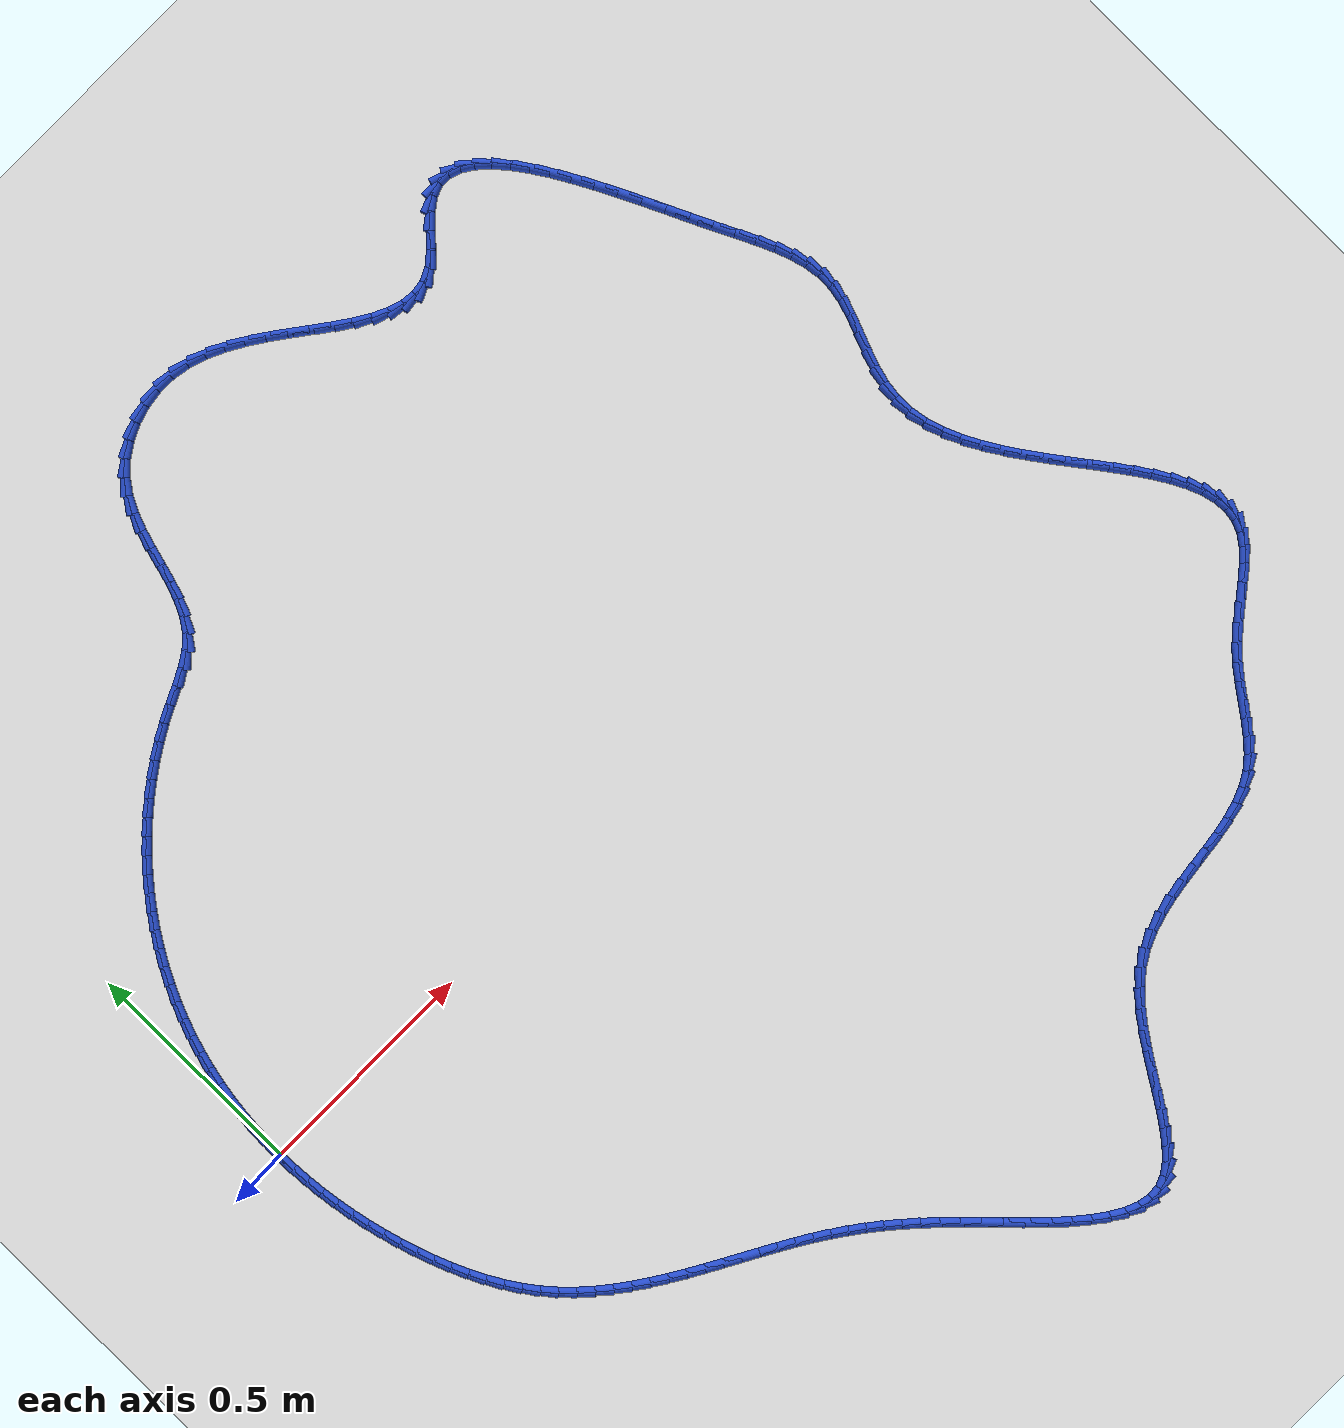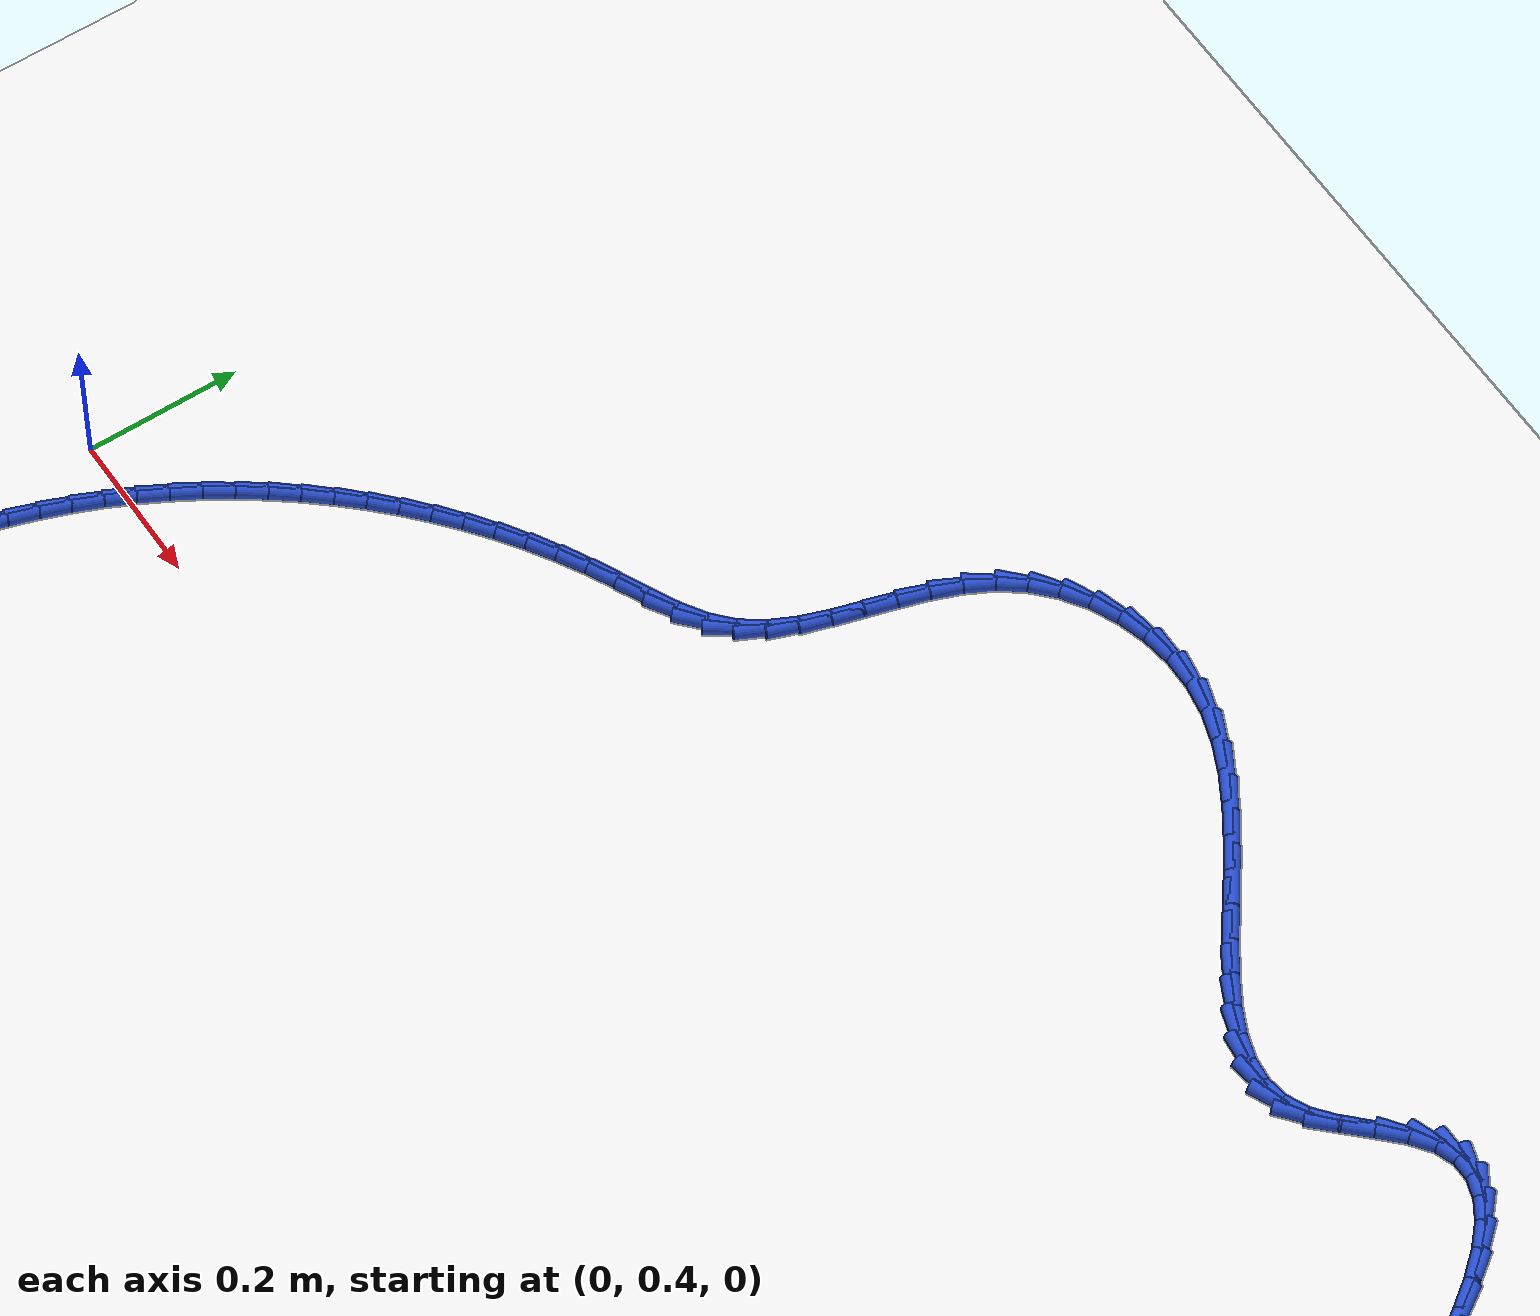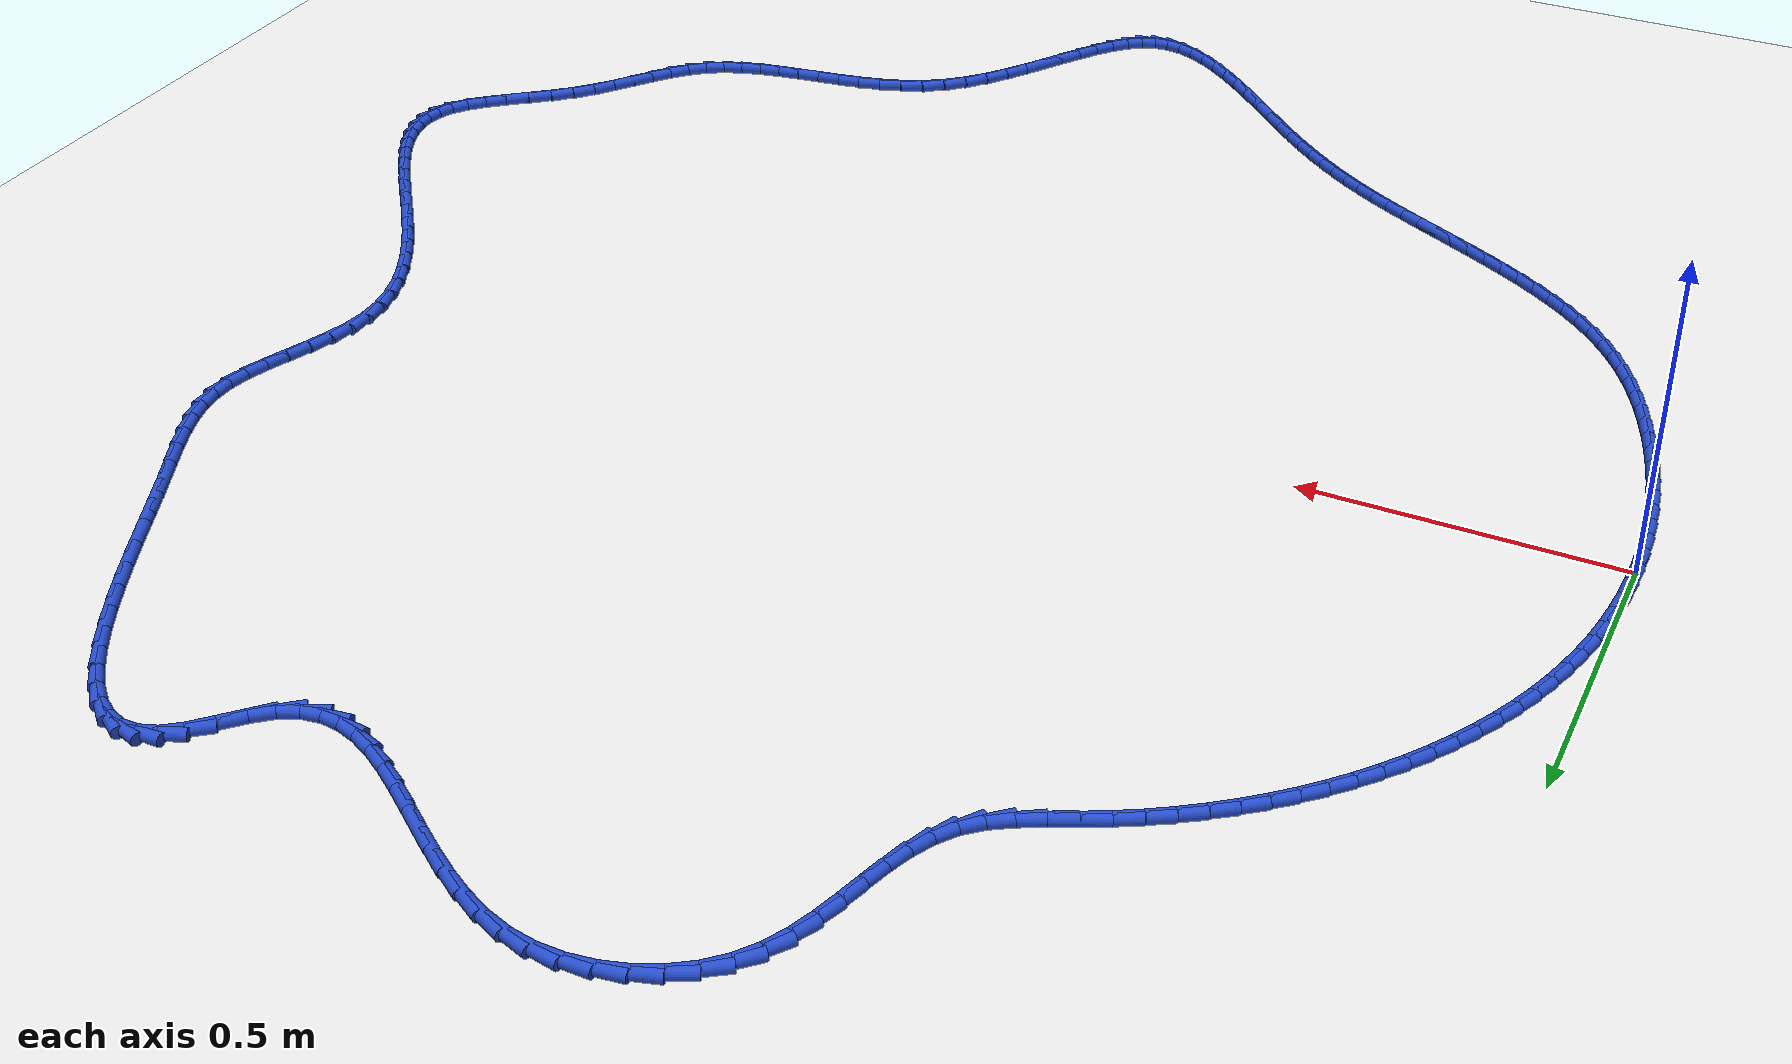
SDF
<sdf version="1.6">
 <world name="default">
  <light name="sun" type="directional">
   <pose>0 0 10 0 -0 0</pose>
   <diffuse>0.8 0.8 0.8 1</diffuse>
   <specular>0.2 0.2 0.2 1</specular>
   <attenuation>
    <range>1000</range>
    <constant>0.9</constant>
    <linear>0.01</linear>
    <quadratic>0.001</quadratic>
   </attenuation>
   <direction>-0.5 0.1 -0.9</direction>
  </light>
  <model name="ground_plane">
   <static>1</static>
   <link name="link">
    <collision name="collision">
     <geometry><plane><normal>0 0 1</normal><size>100 100</size></plane></geometry>
     <surface><friction><ode><mu>100</mu><mu2>50</mu2></ode></friction></surface>
    </collision>
    <visual name="visual">
     <cast_shadows>0</cast_shadows>
     <geometry><plane><normal>0 0 1</normal><size>100 100</size></plane></geometry>
     <material>
      <script><uri>file://media/materials/scripts/gazebo.material</uri><name>Gazebo/WhiteGlow</name></script>
     </material>
    </visual>
   </link>
  </model>
  <gravity>0 0 -9.8</gravity>
  <magnetic_field>6e-06 2.3e-05 -4.2e-05</magnetic_field>
  <atmosphere type="adiabatic"/>
  <physics name="default_physics" default="0" type="ode">
   <max_step_size>0.001</max_step_size>
   <real_time_factor>1</real_time_factor>
   <real_time_update_rate>1000</real_time_update_rate>
  </physics>
  <scene><ambient>0.4 0.4 0.4 1</ambient><background>0.7 0.7 0.7 1</background><shadows>1</shadows></scene>
  <spherical_coordinates>
   <surface_model>EARTH_WGS84</surface_model>
   <latitude_deg>0</latitude_deg>
   <longitude_deg>0</longitude_deg>
   <elevation>0</elevation>
   <heading_deg>0</heading_deg>
  </spherical_coordinates>
  <model name="line">
   <link name="link_0">
    <pose>-1.3010426069826053e-17 3.469446951953614e-17 0.01 0 1.57 1.5600942453260056</pose>
    <collision name="collision">
     <geometry><cylinder><radius>0.01</radius><length>0.08</length></cylinder></geometry>
    </collision>
    <visual name="visual">
     <material>
      <script><name>Gazebo/Blue</name><uri>file://media/materials/scripts/gazebo.material</uri></script>
     </material>
     <geometry><cylinder><radius>0.01</radius><length>0.08</length></cylinder></geometry>
    </visual>
   </link>
   <link name="link_1">
    <pose>0.0004085112136920327 0.03816973534958362 0.01 0 1.57 1.521251000662741</pose>
    <collision name="collision">
     <geometry><cylinder><radius>0.01</radius><length>0.08</length></cylinder></geometry>
    </collision>
    <visual name="visual">
     <material>
      <script><name>Gazebo/Blue</name><uri>file://media/materials/scripts/gazebo.material</uri></script>
     </material>
     <geometry><cylinder><radius>0.01</radius><length>0.08</length></cylinder></geometry>
    </visual>
   </link>
   <link name="link_2">
    <pose>0.0023015739740211098 0.07634717129692392 0.01 0 1.57 1.4816920491337497</pose>
    <collision name="collision">
     <geometry><cylinder><radius>0.01</radius><length>0.08</length></cylinder></geometry>
    </collision>
    <visual name="visual">
     <material>
      <script><name>Gazebo/Blue</name><uri>file://media/materials/scripts/gazebo.material</uri></script>
     </material>
     <geometry><cylinder><radius>0.01</radius><length>0.08</length></cylinder></geometry>
    </visual>
   </link>
   <link name="link_3">
    <pose>0.0057064648923161035 0.11445841700049171 0.01 0 1.57 1.4413207656854696</pose>
    <collision name="collision">
     <geometry><cylinder><radius>0.01</radius><length>0.08</length></cylinder></geometry>
    </collision>
    <visual name="visual">
     <material>
      <script><name>Gazebo/Blue</name><uri>file://media/materials/scripts/gazebo.material</uri></script>
     </material>
     <geometry><cylinder><radius>0.01</radius><length>0.08</length></cylinder></geometry>
    </visual>
   </link>
   <link name="link_4">
    <pose>0.010650460579905903 0.15242958161875791 0.01 0 1.57 1.4000478369320812</pose>
    <collision name="collision">
     <geometry><cylinder><radius>0.01</radius><length>0.08</length></cylinder></geometry>
    </collision>
    <visual name="visual">
     <material>
      <script><name>Gazebo/Blue</name><uri>file://media/materials/scripts/gazebo.material</uri></script>
     </material>
     <geometry><cylinder><radius>0.01</radius><length>0.08</length></cylinder></geometry>
    </visual>
   </link>
   <link name="link_5">
    <pose>0.017160837648119404 0.1901867743101935 0.01 0 1.57 1.357792749813846</pose>
    <collision name="collision">
     <geometry><cylinder><radius>0.01</radius><length>0.08</length></cylinder></geometry>
    </collision>
    <visual name="visual">
     <material>
      <script><name>Gazebo/Blue</name><uri>file://media/materials/scripts/gazebo.material</uri></script>
     </material>
     <geometry><cylinder><radius>0.01</radius><length>0.08</length></cylinder></geometry>
    </visual>
   </link>
   <link name="link_6">
    <pose>0.02526487270828548 0.22765610423326926 0.01 0 1.57 1.3144856001564096</pose>
    <collision name="collision">
     <geometry><cylinder><radius>0.01</radius><length>0.08</length></cylinder></geometry>
    </collision>
    <visual name="visual">
     <material>
      <script><name>Gazebo/Blue</name><uri>file://media/materials/scripts/gazebo.material</uri></script>
     </material>
     <geometry><cylinder><radius>0.01</radius><length>0.08</length></cylinder></geometry>
    </visual>
   </link>
   <link name="link_7">
    <pose>0.03498984237173304 0.26476368054645616 0.01 0 1.57 1.2700692067478376</pose>
    <collision name="collision">
     <geometry><cylinder><radius>0.01</radius><length>0.08</length></cylinder></geometry>
    </collision>
    <visual name="visual">
     <material>
      <script><name>Gazebo/Blue</name><uri>file://media/materials/scripts/gazebo.material</uri></script>
     </material>
     <geometry><cylinder><radius>0.01</radius><length>0.08</length></cylinder></geometry>
    </visual>
   </link>
   <link name="link_8">
    <pose>0.046363023249790934 0.30143561240822503 0.01 0 1.57 1.2246488011370402</pose>
    <collision name="collision">
     <geometry><cylinder><radius>0.01</radius><length>0.08</length></cylinder></geometry>
    </collision>
    <visual name="visual">
     <material>
      <script><name>Gazebo/Blue</name><uri>file://media/materials/scripts/gazebo.material</uri></script>
     </material>
     <geometry><cylinder><radius>0.01</radius><length>0.08</length></cylinder></geometry>
    </visual>
   </link>
   <link name="link_9">
    <pose>0.059406061588320576 0.33759909037641694 0.01 0 1.57 1.1793029908083075</pose>
    <collision name="collision">
     <geometry><cylinder><radius>0.01</radius><length>0.08</length></cylinder></geometry>
    </collision>
    <visual name="visual">
     <material>
      <script><name>Gazebo/Blue</name><uri>file://media/materials/scripts/gazebo.material</uri></script>
     </material>
     <geometry><cylinder><radius>0.01</radius><length>0.08</length></cylinder></geometry>
    </visual>
   </link>
   <link name="link_10">
    <pose>0.07409784828123467 0.37318951684004603 0.01 0 1.57 1.1344804346347401</pose>
    <collision name="collision">
     <geometry><cylinder><radius>0.01</radius><length>0.08</length></cylinder></geometry>
    </collision>
    <visual name="visual">
     <material>
      <script><name>Gazebo/Blue</name><uri>file://media/materials/scripts/gazebo.material</uri></script>
     </material>
     <geometry><cylinder><radius>0.01</radius><length>0.08</length></cylinder></geometry>
    </visual>
   </link>
   <link name="link_11">
    <pose>0.09039765439082144 0.40814606248233115 0.01 0 1.57 1.090109964067773</pose>
    <collision name="collision">
     <geometry><cylinder><radius>0.01</radius><length>0.08</length></cylinder></geometry>
    </collision>
    <visual name="visual">
     <material>
      <script><name>Gazebo/Blue</name><uri>file://media/materials/scripts/gazebo.material</uri></script>
     </material>
     <geometry><cylinder><radius>0.01</radius><length>0.08</length></cylinder></geometry>
    </visual>
   </link>
   <link name="link_12">
    <pose>0.10826464821212468 0.4424079177245401 0.01 0 1.57 1.0461138105548942</pose>
    <collision name="collision">
     <geometry><cylinder><radius>0.01</radius><length>0.08</length></cylinder></geometry>
    </collision>
    <visual name="visual">
     <material>
      <script><name>Gazebo/Blue</name><uri>file://media/materials/scripts/gazebo.material</uri></script>
     </material>
     <geometry><cylinder><radius>0.01</radius><length>0.08</length></cylinder></geometry>
    </visual>
   </link>
   <link name="link_13">
    <pose>0.12765799804018843 0.4759142729879414 0.01 0 1.57 1.0024115345054043</pose>
    <collision name="collision">
     <geometry><cylinder><radius>0.01</radius><length>0.08</length></cylinder></geometry>
    </collision>
    <visual name="visual">
     <material>
      <script><name>Gazebo/Blue</name><uri>file://media/materials/scripts/gazebo.material</uri></script>
     </material>
     <geometry><cylinder><radius>0.01</radius><length>0.08</length></cylinder></geometry>
    </visual>
   </link>
   <link name="link_14">
    <pose>0.14853687217005654 0.5086043186938034 0.01 0 1.57 0.9589211472543481</pose>
    <collision name="collision">
     <geometry><cylinder><radius>0.01</radius><length>0.08</length></cylinder></geometry>
    </collision>
    <visual name="visual">
     <material>
      <script><name>Gazebo/Blue</name><uri>file://media/materials/scripts/gazebo.material</uri></script>
     </material>
     <geometry><cylinder><radius>0.01</radius><length>0.08</length></cylinder></geometry>
    </visual>
   </link>
   <link name="link_15">
    <pose>0.17086043889677272 0.5404172452633939 0.01 0 1.57 0.915560138161888</pose>
    <collision name="collision">
     <geometry><cylinder><radius>0.01</radius><length>0.08</length></cylinder></geometry>
    </collision>
    <visual name="visual">
     <material>
      <script><name>Gazebo/Blue</name><uri>file://media/materials/scripts/gazebo.material</uri></script>
     </material>
     <geometry><cylinder><radius>0.01</radius><length>0.08</length></cylinder></geometry>
    </visual>
   </link>
   <link name="link_16">
    <pose>0.1945878665153811 0.5712922431179818 0.01 0 1.57 0.8722464329653674</pose>
    <collision name="collision">
     <geometry><cylinder><radius>0.01</radius><length>0.08</length></cylinder></geometry>
    </collision>
    <visual name="visual">
     <material>
      <script><name>Gazebo/Blue</name><uri>file://media/materials/scripts/gazebo.material</uri></script>
     </material>
     <geometry><cylinder><radius>0.01</radius><length>0.08</length></cylinder></geometry>
    </visual>
   </link>
   <link name="link_17">
    <pose>0.21967832332092546 0.6011685026788347 0.01 0 1.57 0.8288993104392414</pose>
    <collision name="collision">
     <geometry><cylinder><radius>0.01</radius><length>0.08</length></cylinder></geometry>
    </collision>
    <visual name="visual">
     <material>
      <script><name>Gazebo/Blue</name><uri>file://media/materials/scripts/gazebo.material</uri></script>
     </material>
     <geometry><cylinder><radius>0.01</radius><length>0.08</length></cylinder></geometry>
    </visual>
   </link>
   <link name="link_18">
    <pose>0.24609097760844967 0.6299852143672211 0.01 0 1.57 0.7854403037994284</pose>
    <collision name="collision">
     <geometry><cylinder><radius>0.01</radius><length>0.08</length></cylinder></geometry>
    </collision>
    <visual name="visual">
     <material>
      <script><name>Gazebo/Blue</name><uri>file://media/materials/scripts/gazebo.material</uri></script>
     </material>
     <geometry><cylinder><radius>0.01</radius><length>0.08</length></cylinder></geometry>
    </visual>
   </link>
   <link name="link_19">
    <pose>0.2737849976729976 0.6576815686044093 0.01 0 1.57 0.7417941113048515</pose>
    <collision name="collision">
     <geometry><cylinder><radius>0.01</radius><length>0.08</length></cylinder></geometry>
    </collision>
    <visual name="visual">
     <material>
      <script><name>Gazebo/Blue</name><uri>file://media/materials/scripts/gazebo.material</uri></script>
     </material>
     <geometry><cylinder><radius>0.01</radius><length>0.08</length></cylinder></geometry>
    </visual>
   </link>
   <link name="link_20">
    <pose>0.3027195518096132 0.6841967558116674 0.01 0 1.57 0.6978895372310598</pose>
    <collision name="collision">
     <geometry><cylinder><radius>0.01</radius><length>0.08</length></cylinder></geometry>
    </collision>
    <visual name="visual">
     <material>
      <script><name>Gazebo/Blue</name><uri>file://media/materials/scripts/gazebo.material</uri></script>
     </material>
     <geometry><cylinder><radius>0.01</radius><length>0.08</length></cylinder></geometry>
    </visual>
   </link>
   <link name="link_21">
    <pose>0.3328538083133404 0.7094699664102638 0.01 0 1.57 0.6536604797937026</pose>
    <collision name="collision">
     <geometry><cylinder><radius>0.01</radius><length>0.08</length></cylinder></geometry>
    </collision>
    <visual name="visual">
     <material>
      <script><name>Gazebo/Blue</name><uri>file://media/materials/scripts/gazebo.material</uri></script>
     </material>
     <geometry><cylinder><radius>0.01</radius><length>0.08</length></cylinder></geometry>
    </visual>
   </link>
   <link name="link_22">
    <pose>0.36414693547922306 0.7334403908214668 0.01 0 1.57 0.6090469765927368</pose>
    <collision name="collision">
     <geometry><cylinder><radius>0.01</radius><length>0.08</length></cylinder></geometry>
    </collision>
    <visual name="visual">
     <material>
      <script><name>Gazebo/Blue</name><uri>file://media/materials/scripts/gazebo.material</uri></script>
     </material>
     <geometry><cylinder><radius>0.01</radius><length>0.08</length></cylinder></geometry>
    </visual>
   </link>
   <link name="link_23">
    <pose>0.396558101602305 0.7560472194665443 0.01 0 1.57 0.5639963106220793</pose>
    <collision name="collision">
     <geometry><cylinder><radius>0.01</radius><length>0.08</length></cylinder></geometry>
    </collision>
    <visual name="visual">
     <material>
      <script><name>Gazebo/Blue</name><uri>file://media/materials/scripts/gazebo.material</uri></script>
     </material>
     <geometry><cylinder><radius>0.01</radius><length>0.08</length></cylinder></geometry>
    </visual>
   </link>
   <link name="link_24">
    <pose>0.43004647497763004 0.7772296427667649 0.01 0 1.57 0.5184641707763226</pose>
    <collision name="collision">
     <geometry><cylinder><radius>0.01</radius><length>0.08</length></cylinder></geometry>
    </collision>
    <visual name="visual">
     <material>
      <script><name>Gazebo/Blue</name><uri>file://media/materials/scripts/gazebo.material</uri></script>
     </material>
     <geometry><cylinder><radius>0.01</radius><length>0.08</length></cylinder></geometry>
    </visual>
   </link>
   <link name="link_25">
    <pose>0.46457122390024225 0.7969268511433965 0.01 0 1.57 0.4724509050586902</pose>
    <collision name="collision">
     <geometry><cylinder><radius>0.01</radius><length>0.08</length></cylinder></geometry>
    </collision>
    <visual name="visual">
     <material>
      <script><name>Gazebo/Blue</name><uri>file://media/materials/scripts/gazebo.material</uri></script>
     </material>
     <geometry><cylinder><radius>0.01</radius><length>0.08</length></cylinder></geometry>
    </visual>
   </link>
   <link name="link_26">
    <pose>0.5000904836647061 0.8150790774380501 0.01 0 1.57 0.4419052265983376</pose>
    <collision name="collision">
     <geometry><cylinder><radius>0.01</radius><length>0.08</length></cylinder></geometry>
    </collision>
    <visual name="visual">
     <material>
      <script><name>Gazebo/Blue</name><uri>file://media/materials/scripts/gazebo.material</uri></script>
     </material>
     <geometry><cylinder><radius>0.01</radius><length>0.08</length></cylinder></geometry>
    </visual>
   </link>
   <link name="link_27">
    <pose>0.5360848990232084 0.8321083992394709 0.01 0 1.57 0.46861760996024854</pose>
    <collision name="collision">
     <geometry><cylinder><radius>0.01</radius><length>0.08</length></cylinder></geometry>
    </collision>
    <visual name="visual">
     <material>
      <script><name>Gazebo/Blue</name><uri>file://media/materials/scripts/gazebo.material</uri></script>
     </material>
     <geometry><cylinder><radius>0.01</radius><length>0.08</length></cylinder></geometry>
    </visual>
   </link>
   <link name="link_28">
    <pose>0.5708007360729581 0.8496825290089063 0.01 0 1.57 0.5655586599083128</pose>
    <collision name="collision">
     <geometry><cylinder><radius>0.01</radius><length>0.08</length></cylinder></geometry>
    </collision>
    <visual name="visual">
     <material>
      <script><name>Gazebo/Blue</name><uri>file://media/materials/scripts/gazebo.material</uri></script>
     </material>
     <geometry><cylinder><radius>0.01</radius><length>0.08</length></cylinder></geometry>
    </visual>
   </link>
   <link name="link_29">
    <pose>0.6022874500627845 0.8696677847611255 0.01 0 1.57 0.7439870550854325</pose>
    <collision name="collision">
     <geometry><cylinder><radius>0.01</radius><length>0.08</length></cylinder></geometry>
    </collision>
    <visual name="visual">
     <material>
      <script><name>Gazebo/Blue</name><uri>file://media/materials/scripts/gazebo.material</uri></script>
     </material>
     <geometry><cylinder><radius>0.01</radius><length>0.08</length></cylinder></geometry>
    </visual>
   </link>
   <link name="link_30">
    <pose>0.6286216127380578 0.8939064717160263 0.01 0 1.57 0.9569951795448739</pose>
    <collision name="collision">
     <geometry><cylinder><radius>0.01</radius><length>0.08</length></cylinder></geometry>
    </collision>
    <visual name="visual">
     <material>
      <script><name>Gazebo/Blue</name><uri>file://media/materials/scripts/gazebo.material</uri></script>
     </material>
     <geometry><cylinder><radius>0.01</radius><length>0.08</length></cylinder></geometry>
    </visual>
   </link>
   <link name="link_31">
    <pose>0.6491823064881527 0.9230874672947679 0.01 0 1.57 1.1209489093276608</pose>
    <collision name="collision">
     <geometry><cylinder><radius>0.01</radius><length>0.08</length></cylinder></geometry>
    </collision>
    <visual name="visual">
     <material>
      <script><name>Gazebo/Blue</name><uri>file://media/materials/scripts/gazebo.material</uri></script>
     </material>
     <geometry><cylinder><radius>0.01</radius><length>0.08</length></cylinder></geometry>
    </visual>
   </link>
   <link name="link_32">
    <pose>0.6652002141731684 0.9562599790509966 0.01 0 1.57 1.2287956257395467</pose>
    <collision name="collision">
     <geometry><cylinder><radius>0.01</radius><length>0.08</length></cylinder></geometry>
    </collision>
    <visual name="visual">
     <material>
      <script><name>Gazebo/Blue</name><uri>file://media/materials/scripts/gazebo.material</uri></script>
     </material>
     <geometry><cylinder><radius>0.01</radius><length>0.08</length></cylinder></geometry>
    </visual>
   </link>
   <link name="link_33">
    <pose>0.6780472304885745 0.9923481655361286 0.01 0 1.57 1.2873501964820488</pose>
    <collision name="collision">
     <geometry><cylinder><radius>0.01</radius><length>0.08</length></cylinder></geometry>
    </collision>
    <visual name="visual">
     <material>
      <script><name>Gazebo/Blue</name><uri>file://media/materials/scripts/gazebo.material</uri></script>
     </material>
     <geometry><cylinder><radius>0.01</radius><length>0.08</length></cylinder></geometry>
    </visual>
   </link>
   <link name="link_34">
    <pose>0.6890952501298401 1.030276185301581 0.01 0 1.57 1.3028959711552246</pose>
    <collision name="collision">
     <geometry><cylinder><radius>0.01</radius><length>0.08</length></cylinder></geometry>
    </collision>
    <visual name="visual">
     <material>
      <script><name>Gazebo/Blue</name><uri>file://media/materials/scripts/gazebo.material</uri></script>
     </material>
     <geometry><cylinder><radius>0.01</radius><length>0.08</length></cylinder></geometry>
    </visual>
   </link>
   <link name="link_35">
    <pose>0.6997161677924342 1.0689681968987708 0.01 0 1.57 1.2781050779983438</pose>
    <collision name="collision">
     <geometry><cylinder><radius>0.01</radius><length>0.08</length></cylinder></geometry>
    </collision>
    <visual name="visual">
     <material>
      <script><name>Gazebo/Blue</name><uri>file://media/materials/scripts/gazebo.material</uri></script>
     </material>
     <geometry><cylinder><radius>0.01</radius><length>0.08</length></cylinder></geometry>
    </visual>
   </link>
   <link name="link_36">
    <pose>0.7112818781718255 1.1073483588791135 0.01 0 1.57 1.2117834386769326</pose>
    <collision name="collision">
     <geometry><cylinder><radius>0.01</radius><length>0.08</length></cylinder></geometry>
    </collision>
    <visual name="visual">
     <material>
      <script><name>Gazebo/Blue</name><uri>file://media/materials/scripts/gazebo.material</uri></script>
     </material>
     <geometry><cylinder><radius>0.01</radius><length>0.08</length></cylinder></geometry>
    </visual>
   </link>
   <link name="link_37">
    <pose>0.725164275963484 1.1443408297940274 0.01 0 1.57 1.1000724248696783</pose>
    <collision name="collision">
     <geometry><cylinder><radius>0.01</radius><length>0.08</length></cylinder></geometry>
    </collision>
    <visual name="visual">
     <material>
      <script><name>Gazebo/Blue</name><uri>file://media/materials/scripts/gazebo.material</uri></script>
     </material>
     <geometry><cylinder><radius>0.01</radius><length>0.08</length></cylinder></geometry>
    </visual>
   </link>
   <link name="link_38">
    <pose>0.742735255862878 1.1788697681949283 0.01 0 1.57 0.940819987587876</pose>
    <collision name="collision">
     <geometry><cylinder><radius>0.01</radius><length>0.08</length></cylinder></geometry>
    </collision>
    <visual name="visual">
     <material>
      <script><name>Gazebo/Blue</name><uri>file://media/materials/scripts/gazebo.material</uri></script>
     </material>
     <geometry><cylinder><radius>0.01</radius><length>0.08</length></cylinder></geometry>
    </visual>
   </link>
   <link name="link_39">
    <pose>0.7653358899972498 1.2098686721806822 0.01 0 1.57 0.7623331683758221</pose>
    <collision name="collision">
     <geometry><cylinder><radius>0.01</radius><length>0.08</length></cylinder></geometry>
    </collision>
    <visual name="visual">
     <material>
      <script><name>Gazebo/Blue</name><uri>file://media/materials/scripts/gazebo.material</uri></script>
     </material>
     <geometry><cylinder><radius>0.01</radius><length>0.08</length></cylinder></geometry>
    </visual>
   </link>
   <link name="link_40">
    <pose>0.7933036446946121 1.2365751424775655 0.01 0 1.57 0.5958100581250614</pose>
    <collision name="collision">
     <geometry><cylinder><radius>0.01</radius><length>0.08</length></cylinder></geometry>
    </collision>
    <visual name="visual">
     <material>
      <script><name>Gazebo/Blue</name><uri>file://media/materials/scripts/gazebo.material</uri></script>
     </material>
     <geometry><cylinder><radius>0.01</radius><length>0.08</length></cylinder></geometry>
    </visual>
   </link>
   <link name="link_41">
    <pose>0.8257748582365394 1.258590733662124 0.01 0 1.57 0.4395600535404526</pose>
    <collision name="collision">
     <geometry><cylinder><radius>0.01</radius><length>0.08</length></cylinder></geometry>
    </collision>
    <visual name="visual">
     <material>
      <script><name>Gazebo/Blue</name><uri>file://media/materials/scripts/gazebo.material</uri></script>
     </material>
     <geometry><cylinder><radius>0.01</radius><length>0.08</length></cylinder></geometry>
    </visual>
   </link>
   <link name="link_42">
    <pose>0.8618151417294005 1.2755384313546707 0.01 0 1.57 0.28909008916874357</pose>
    <collision name="collision">
     <geometry><cylinder><radius>0.01</radius><length>0.08</length></cylinder></geometry>
    </collision>
    <visual name="visual">
     <material>
      <script><name>Gazebo/Blue</name><uri>file://media/materials/scripts/gazebo.material</uri></script>
     </material>
     <geometry><cylinder><radius>0.01</radius><length>0.08</length></cylinder></geometry>
    </visual>
   </link>
   <link name="link_43">
    <pose>0.9004901062795648 1.2870412211755184 0.01 0 1.57 0.1397840937089755</pose>
    <collision name="collision">
     <geometry><cylinder><radius>0.01</radius><length>0.08</length></cylinder></geometry>
    </collision>
    <visual name="visual">
     <material>
      <script><name>Gazebo/Blue</name><uri>file://media/materials/scripts/gazebo.material</uri></script>
     </material>
     <geometry><cylinder><radius>0.01</radius><length>0.08</length></cylinder></geometry>
    </visual>
   </link>
   <link name="link_44">
    <pose>0.9408653629934016 1.2927220887449808 0.01 0 1.57 -0.012591810268285411</pose>
    <collision name="collision">
     <geometry><cylinder><radius>0.01</radius><length>0.08</length></cylinder></geometry>
    </collision>
    <visual name="visual">
     <material>
      <script><name>Gazebo/Blue</name><uri>file://media/materials/scripts/gazebo.material</uri></script>
     </material>
     <geometry><cylinder><radius>0.01</radius><length>0.08</length></cylinder></geometry>
    </visual>
   </link>
   <link name="link_45">
    <pose>0.9820065229772797 1.2922040196833708 0.01 0 1.57 -0.17096162779130247</pose>
    <collision name="collision">
     <geometry><cylinder><radius>0.01</radius><length>0.08</length></cylinder></geometry>
    </collision>
    <visual name="visual">
     <material>
      <script><name>Gazebo/Blue</name><uri>file://media/materials/scripts/gazebo.material</uri></script>
     </material>
     <geometry><cylinder><radius>0.01</radius><length>0.08</length></cylinder></geometry>
    </visual>
   </link>
   <link name="link_46">
    <pose>1.022989888986764 1.2851283665782518 0.01 0 1.57 -0.31942416145211083</pose>
    <collision name="collision">
     <geometry><cylinder><radius>0.01</radius><length>0.08</length></cylinder></geometry>
    </collision>
    <visual name="visual">
     <material>
      <script><name>Gazebo/Blue</name><uri>file://media/materials/scripts/gazebo.material</uri></script>
     </material>
     <geometry><cylinder><radius>0.01</radius><length>0.08</length></cylinder></geometry>
    </visual>
   </link>
   <link name="link_47">
    <pose>1.0632794967661048 1.2718025606524432 0.01 0 1.57 -0.43609325064968757</pose>
    <collision name="collision">
     <geometry><cylinder><radius>0.01</radius><length>0.08</length></cylinder></geometry>
    </collision>
    <visual name="visual">
     <material>
      <script><name>Gazebo/Blue</name><uri>file://media/materials/scripts/gazebo.material</uri></script>
     </material>
     <geometry><cylinder><radius>0.01</radius><length>0.08</length></cylinder></geometry>
    </visual>
   </link>
   <link name="link_48">
    <pose>1.1028274870869748 1.2533725388531043 0.01 0 1.57 -0.5224317070120871</pose>
    <collision name="collision">
     <geometry><cylinder><radius>0.01</radius><length>0.08</length></cylinder></geometry>
    </collision>
    <visual name="visual">
     <material>
      <script><name>Gazebo/Blue</name><uri>file://media/materials/scripts/gazebo.material</uri></script>
     </material>
     <geometry><cylinder><radius>0.01</radius><length>0.08</length></cylinder></geometry>
    </visual>
   </link>
   <link name="link_49">
    <pose>1.1416171008792753 1.2310376644582781 0.01 0 1.57 -0.5824710841185692</pose>
    <collision name="collision">
     <geometry><cylinder><radius>0.01</radius><length>0.08</length></cylinder></geometry>
    </collision>
    <visual name="visual">
     <material>
      <script><name>Gazebo/Blue</name><uri>file://media/materials/scripts/gazebo.material</uri></script>
     </material>
     <geometry><cylinder><radius>0.01</radius><length>0.08</length></cylinder></geometry>
    </visual>
   </link>
   <link name="link_50">
    <pose>1.1796315790729062 1.205997300746008 0.01 0 1.57 -0.6195185014129785</pose>
    <collision name="collision">
     <geometry><cylinder><radius>0.01</radius><length>0.08</length></cylinder></geometry>
    </collision>
    <visual name="visual">
     <material>
      <script><name>Gazebo/Blue</name><uri>file://media/materials/scripts/gazebo.material</uri></script>
     </material>
     <geometry><cylinder><radius>0.01</radius><length>0.08</length></cylinder></geometry>
    </visual>
   </link>
   <link name="link_51">
    <pose>1.2168541625977678 1.179450810994337 0.01 0 1.57 -0.63541704887677</pose>
    <collision name="collision">
     <geometry><cylinder><radius>0.01</radius><length>0.08</length></cylinder></geometry>
    </collision>
    <visual name="visual">
     <material>
      <script><name>Gazebo/Blue</name><uri>file://media/materials/scripts/gazebo.material</uri></script>
     </material>
     <geometry><cylinder><radius>0.01</radius><length>0.08</length></cylinder></geometry>
    </visual>
   </link>
   <link name="link_52">
    <pose>1.2532680923837614 1.1525975584813082 0.01 0 1.57 -0.6302300221924924</pose>
    <collision name="collision">
     <geometry><cylinder><radius>0.01</radius><length>0.08</length></cylinder></geometry>
    </collision>
    <visual name="visual">
     <material>
      <script><name>Gazebo/Blue</name><uri>file://media/materials/scripts/gazebo.material</uri></script>
     </material>
     <geometry><cylinder><radius>0.01</radius><length>0.08</length></cylinder></geometry>
    </visual>
   </link>
   <link name="link_53">
    <pose>1.288856609360786 1.1266369064849646 0.01 0 1.57 -0.6019076443133381</pose>
    <collision name="collision">
     <geometry><cylinder><radius>0.01</radius><length>0.08</length></cylinder></geometry>
    </collision>
    <visual name="visual">
     <material>
      <script><name>Gazebo/Blue</name><uri>file://media/materials/scripts/gazebo.material</uri></script>
     </material>
     <geometry><cylinder><radius>0.01</radius><length>0.08</length></cylinder></geometry>
    </visual>
   </link>
   <link name="link_54">
    <pose>1.3236029544587427 1.1027682182833496 0.01 0 1.57 -0.5457167110879396</pose>
    <collision name="collision">
     <geometry><cylinder><radius>0.01</radius><length>0.08</length></cylinder></geometry>
    </collision>
    <visual name="visual">
     <material>
      <script><name>Gazebo/Blue</name><uri>file://media/materials/scripts/gazebo.material</uri></script>
     </material>
     <geometry><cylinder><radius>0.01</radius><length>0.08</length></cylinder></geometry>
    </visual>
   </link>
   <link name="link_55">
    <pose>1.3574903686075324 1.082190857154506 0.01 0 1.57 -0.45343749786819115</pose>
    <collision name="collision">
     <geometry><cylinder><radius>0.01</radius><length>0.08</length></cylinder></geometry>
    </collision>
    <visual name="visual">
     <material>
      <script><name>Gazebo/Blue</name><uri>file://media/materials/scripts/gazebo.material</uri></script>
     </material>
     <geometry><cylinder><radius>0.01</radius><length>0.08</length></cylinder></geometry>
    </visual>
   </link>
   <link name="link_56">
    <pose>1.3905020927370542 1.0661041863764766 0.01 0 1.57 -0.3130445924595224</pose>
    <collision name="collision">
     <geometry><cylinder><radius>0.01</radius><length>0.08</length></cylinder></geometry>
    </collision>
    <visual name="visual">
     <material>
      <script><name>Gazebo/Blue</name><uri>file://media/materials/scripts/gazebo.material</uri></script>
     </material>
     <geometry><cylinder><radius>0.01</radius><length>0.08</length></cylinder></geometry>
    </visual>
   </link>
   <link name="link_57">
    <pose>1.42262136777721 1.055707569227306 0.01 0 1.57 -0.11190454134681728</pose>
    <collision name="collision">
     <geometry><cylinder><radius>0.01</radius><length>0.08</length></cylinder></geometry>
    </collision>
    <visual name="visual">
     <material>
      <script><name>Gazebo/Blue</name><uri>file://media/materials/scripts/gazebo.material</uri></script>
     </material>
     <geometry><cylinder><radius>0.01</radius><length>0.08</length></cylinder></geometry>
    </visual>
   </link>
   <link name="link_58">
    <pose>1.4538314346578982 1.0522003689850354 0.01 0 1.57 0.15014804553716435</pose>
    <collision name="collision">
     <geometry><cylinder><radius>0.01</radius><length>0.08</length></cylinder></geometry>
    </collision>
    <visual name="visual">
     <material>
      <script><name>Gazebo/Blue</name><uri>file://media/materials/scripts/gazebo.material</uri></script>
     </material>
     <geometry><cylinder><radius>0.01</radius><length>0.08</length></cylinder></geometry>
    </visual>
   </link>
   <link name="link_59">
    <pose>1.4841155343090215 1.056781948927709 0.01 0 1.57 0.44157163698915336</pose>
    <collision name="collision">
     <geometry><cylinder><radius>0.01</radius><length>0.08</length></cylinder></geometry>
    </collision>
    <visual name="visual">
     <material>
      <script><name>Gazebo/Blue</name><uri>file://media/materials/scripts/gazebo.material</uri></script>
     </material>
     <geometry><cylinder><radius>0.01</radius><length>0.08</length></cylinder></geometry>
    </visual>
   </link>
   <link name="link_60">
    <pose>1.5134569076604787 1.0706516723333699 0.01 0 1.57 0.6926914523672263</pose>
    <collision name="collision">
     <geometry><cylinder><radius>0.01</radius><length>0.08</length></cylinder></geometry>
    </collision>
    <visual name="visual">
     <material>
      <script><name>Gazebo/Blue</name><uri>file://media/materials/scripts/gazebo.material</uri></script>
     </material>
     <geometry><cylinder><radius>0.01</radius><length>0.08</length></cylinder></geometry>
    </visual>
   </link>
   <link name="link_61">
    <pose>1.5418664681859418 1.0942279428747947 0.01 0 1.57 0.8051517234412948</pose>
    <collision name="collision">
     <geometry><cylinder><radius>0.01</radius><length>0.08</length></cylinder></geometry>
    </collision>
    <visual name="visual">
     <material>
      <script><name>Gazebo/Blue</name><uri>file://media/materials/scripts/gazebo.material</uri></script>
     </material>
     <geometry><cylinder><radius>0.01</radius><length>0.08</length></cylinder></geometry>
    </visual>
   </link>
   <link name="link_62">
    <pose>1.569529573038283 1.123006108795517 0.01 0 1.57 0.7925659561017157</pose>
    <collision name="collision">
     <geometry><cylinder><radius>0.01</radius><length>0.08</length></cylinder></geometry>
    </collision>
    <visual name="visual">
     <material>
      <script><name>Gazebo/Blue</name><uri>file://media/materials/scripts/gazebo.material</uri></script>
     </material>
     <geometry><cylinder><radius>0.01</radius><length>0.08</length></cylinder></geometry>
    </visual>
   </link>
   <link name="link_63">
    <pose>1.596699375072815 1.1505682245900453 0.01 0 1.57 0.6402516160420375</pose>
    <collision name="collision">
     <geometry><cylinder><radius>0.01</radius><length>0.08</length></cylinder></geometry>
    </collision>
    <visual name="visual">
     <material>
      <script><name>Gazebo/Blue</name><uri>file://media/materials/scripts/gazebo.material</uri></script>
     </material>
     <geometry><cylinder><radius>0.01</radius><length>0.08</length></cylinder></geometry>
    </visual>
   </link>
   <link name="link_64">
    <pose>1.6236238781954746 1.170625229156104 0.01 0 1.57 0.34636034771015345</pose>
    <collision name="collision">
     <geometry><cylinder><radius>0.01</radius><length>0.08</length></cylinder></geometry>
    </collision>
    <visual name="visual">
     <material>
      <script><name>Gazebo/Blue</name><uri>file://media/materials/scripts/gazebo.material</uri></script>
     </material>
     <geometry><cylinder><radius>0.01</radius><length>0.08</length></cylinder></geometry>
    </visual>
   </link>
   <link name="link_65">
    <pose>1.6504154880556818 1.1802945710826445 0.01 0 1.57 0.0003223808804786411</pose>
    <collision name="collision">
     <geometry><cylinder><radius>0.01</radius><length>0.08</length></cylinder></geometry>
    </collision>
    <visual name="visual">
     <material>
      <script><name>Gazebo/Blue</name><uri>file://media/materials/scripts/gazebo.material</uri></script>
     </material>
     <geometry><cylinder><radius>0.01</radius><length>0.08</length></cylinder></geometry>
    </visual>
   </link>
   <link name="link_66">
    <pose>1.6770429336290438 1.1803031552622907 0.01 0 1.57 -0.319812314716839</pose>
    <collision name="collision">
     <geometry><cylinder><radius>0.01</radius><length>0.08</length></cylinder></geometry>
    </collision>
    <visual name="visual">
     <material>
      <script><name>Gazebo/Blue</name><uri>file://media/materials/scripts/gazebo.material</uri></script>
     </material>
     <geometry><cylinder><radius>0.01</radius><length>0.08</length></cylinder></geometry>
    </visual>
   </link>
   <link name="link_67">
    <pose>1.7034680265985784 1.1715516633370364 0.01 0 1.57 -0.5653141672963753</pose>
    <collision name="collision">
     <geometry><cylinder><radius>0.01</radius><length>0.08</length></cylinder></geometry>
    </collision>
    <visual name="visual">
     <material>
      <script><name>Gazebo/Blue</name><uri>file://media/materials/scripts/gazebo.material</uri></script>
     </material>
     <geometry><cylinder><radius>0.01</radius><length>0.08</length></cylinder></geometry>
    </visual>
   </link>
   <link name="link_68">
    <pose>1.7296525786473043 1.1549407769488762 0.01 0 1.57 -0.738213329936311</pose>
    <collision name="collision">
     <geometry><cylinder><radius>0.01</radius><length>0.08</length></cylinder></geometry>
    </collision>
    <visual name="visual">
     <material>
      <script><name>Gazebo/Blue</name><uri>file://media/materials/scripts/gazebo.material</uri></script>
     </material>
     <geometry><cylinder><radius>0.01</radius><length>0.08</length></cylinder></geometry>
    </visual>
   </link>
   <link name="link_69">
    <pose>1.7555584014582404 1.1313711777398059 0.01 0 1.57 -0.8584115421069373</pose>
    <collision name="collision">
     <geometry><cylinder><radius>0.01</radius><length>0.08</length></cylinder></geometry>
    </collision>
    <visual name="visual">
     <material>
      <script><name>Gazebo/Blue</name><uri>file://media/materials/scripts/gazebo.material</uri></script>
     </material>
     <geometry><cylinder><radius>0.01</radius><length>0.08</length></cylinder></geometry>
    </visual>
   </link>
   <link name="link_70">
    <pose>1.7811473067144044 1.1017435473518191 0.01 0 1.57 -0.9432113997576469</pose>
    <collision name="collision">
     <geometry><cylinder><radius>0.01</radius><length>0.08</length></cylinder></geometry>
    </collision>
    <visual name="visual">
     <material>
      <script><name>Gazebo/Blue</name><uri>file://media/materials/scripts/gazebo.material</uri></script>
     </material>
     <geometry><cylinder><radius>0.01</radius><length>0.08</length></cylinder></geometry>
    </visual>
   </link>
   <link name="link_71">
    <pose>1.8063811060988149 1.0669585674269109 0.01 0 1.57 -1.0041433141635454</pose>
    <collision name="collision">
     <geometry><cylinder><radius>0.01</radius><length>0.08</length></cylinder></geometry>
    </collision>
    <visual name="visual">
     <material>
      <script><name>Gazebo/Blue</name><uri>file://media/materials/scripts/gazebo.material</uri></script>
     </material>
     <geometry><cylinder><radius>0.01</radius><length>0.08</length></cylinder></geometry>
    </visual>
   </link>
   <link name="link_72">
    <pose>1.8312216112944915 1.0279169196070757 0.01 0 1.57 -1.0484236529388244</pose>
    <collision name="collision">
     <geometry><cylinder><radius>0.01</radius><length>0.08</length></cylinder></geometry>
    </collision>
    <visual name="visual">
     <material>
      <script><name>Gazebo/Blue</name><uri>file://media/materials/scripts/gazebo.material</uri></script>
     </material>
     <geometry><cylinder><radius>0.01</radius><length>0.08</length></cylinder></geometry>
    </visual>
   </link>
   <link name="link_73">
    <pose>1.8556306339844517 0.9855192855343082 0.01 0 1.57 -1.0805303510151576</pose>
    <collision name="collision">
     <geometry><cylinder><radius>0.01</radius><length>0.08</length></cylinder></geometry>
    </collision>
    <visual name="visual">
     <material>
      <script><name>Gazebo/Blue</name><uri>file://media/materials/scripts/gazebo.material</uri></script>
     </material>
     <geometry><cylinder><radius>0.01</radius><length>0.08</length></cylinder></geometry>
    </visual>
   </link>
   <link name="link_74">
    <pose>1.8795699858517145 0.9406663468506029 0.01 0 1.57 -1.1032309996872613</pose>
    <collision name="collision">
     <geometry><cylinder><radius>0.01</radius><length>0.08</length></cylinder></geometry>
    </collision>
    <visual name="visual">
     <material>
      <script><name>Gazebo/Blue</name><uri>file://media/materials/scripts/gazebo.material</uri></script>
     </material>
     <geometry><cylinder><radius>0.01</radius><length>0.08</length></cylinder></geometry>
    </visual>
   </link>
   <link name="link_75">
    <pose>1.903001478579298 0.8942587851979545 0.01 0 1.57 -1.1181783493141353</pose>
    <collision name="collision">
     <geometry><cylinder><radius>0.01</radius><length>0.08</length></cylinder></geometry>
    </collision>
    <visual name="visual">
     <material>
      <script><name>Gazebo/Blue</name><uri>file://media/materials/scripts/gazebo.material</uri></script>
     </material>
     <geometry><cylinder><radius>0.01</radius><length>0.08</length></cylinder></geometry>
    </visual>
   </link>
   <link name="link_76">
    <pose>1.925886923850221 0.847197282218358 0.01 0 1.57 -1.126229724855709</pose>
    <collision name="collision">
     <geometry><cylinder><radius>0.01</radius><length>0.08</length></cylinder></geometry>
    </collision>
    <visual name="visual">
     <material>
      <script><name>Gazebo/Blue</name><uri>file://media/materials/scripts/gazebo.material</uri></script>
     </material>
     <geometry><cylinder><radius>0.01</radius><length>0.08</length></cylinder></geometry>
    </visual>
   </link>
   <link name="link_77">
    <pose>1.9481881333475022 0.8003825195538076 0.01 0 1.57 -1.1275838786068733</pose>
    <collision name="collision">
     <geometry><cylinder><radius>0.01</radius><length>0.08</length></cylinder></geometry>
    </collision>
    <visual name="visual">
     <material>
      <script><name>Gazebo/Blue</name><uri>file://media/materials/scripts/gazebo.material</uri></script>
     </material>
     <geometry><cylinder><radius>0.01</radius><length>0.08</length></cylinder></geometry>
    </visual>
   </link>
   <link name="link_78">
    <pose>1.969866918754159 0.7547151788462978 0.01 0 1.57 -1.121769330073949</pose>
    <collision name="collision">
     <geometry><cylinder><radius>0.01</radius><length>0.08</length></cylinder></geometry>
    </collision>
    <visual name="visual">
     <material>
      <script><name>Gazebo/Blue</name><uri>file://media/materials/scripts/gazebo.material</uri></script>
     </material>
     <geometry><cylinder><radius>0.01</radius><length>0.08</length></cylinder></geometry>
    </visual>
   </link>
   <link name="link_79">
    <pose>1.9908850917159027 0.7110959416665071 0.01 0 1.57 -1.1123186171506994</pose>
    <collision name="collision">
     <geometry><cylinder><radius>0.01</radius><length>0.08</length></cylinder></geometry>
    </collision>
    <visual name="visual">
     <material>
      <script><name>Gazebo/Blue</name><uri>file://media/materials/scripts/gazebo.material</uri></script>
     </material>
     <geometry><cylinder><radius>0.01</radius><length>0.08</length></cylinder></geometry>
    </visual>
   </link>
   <link name="link_80">
    <pose>2.011077731548608 0.6701832342266626 0.01 0 1.57 -1.118504741108917</pose>
    <collision name="collision">
     <geometry><cylinder><radius>0.01</radius><length>0.08</length></cylinder></geometry>
    </collision>
    <visual name="visual">
     <material>
      <script><name>Gazebo/Blue</name><uri>file://media/materials/scripts/gazebo.material</uri></script>
     </material>
     <geometry><cylinder><radius>0.01</radius><length>0.08</length></cylinder></geometry>
    </visual>
   </link>
   <link name="link_81">
    <pose>2.0297830705706748 0.6316857341813379 0.01 0 1.57 -1.1488132450318516</pose>
    <collision name="collision">
     <geometry><cylinder><radius>0.01</radius><length>0.08</length></cylinder></geometry>
    </collision>
    <visual name="visual">
     <material>
      <script><name>Gazebo/Blue</name><uri>file://media/materials/scripts/gazebo.material</uri></script>
     </material>
     <geometry><cylinder><radius>0.01</radius><length>0.08</length></cylinder></geometry>
    </visual>
   </link>
   <link name="link_82">
    <pose>2.046217599997772 0.5950794048136564 0.01 0 1.57 -1.2079142531775957</pose>
    <collision name="collision">
     <geometry><cylinder><radius>0.01</radius><length>0.08</length></cylinder></geometry>
    </collision>
    <visual name="visual">
     <material>
      <script><name>Gazebo/Blue</name><uri>file://media/materials/scripts/gazebo.material</uri></script>
     </material>
     <geometry><cylinder><radius>0.01</radius><length>0.08</length></cylinder></geometry>
    </visual>
   </link>
   <link name="link_83">
    <pose>2.059597811045568 0.5598402094067411 0.01 0 1.57 -1.3001757621355365</pose>
    <collision name="collision">
     <geometry><cylinder><radius>0.01</radius><length>0.08</length></cylinder></geometry>
    </collision>
    <visual name="visual">
     <material>
      <script><name>Gazebo/Blue</name><uri>file://media/materials/scripts/gazebo.material</uri></script>
     </material>
     <geometry><cylinder><radius>0.01</radius><length>0.08</length></cylinder></geometry>
    </visual>
   </link>
   <link name="link_84">
    <pose>2.069140194929732 0.5254441112437157 0.01 0 1.57 -1.4273782947889486</pose>
    <collision name="collision">
     <geometry><cylinder><radius>0.01</radius><length>0.08</length></cylinder></geometry>
    </collision>
    <visual name="visual">
     <material>
      <script><name>Gazebo/Blue</name><uri>file://media/materials/scripts/gazebo.material</uri></script>
     </material>
     <geometry><cylinder><radius>0.01</radius><length>0.08</length></cylinder></geometry>
    </visual>
   </link>
   <link name="link_85">
    <pose>2.0740612428659335 0.4913670736077029 0.01 0 1.57 1.5566850005064563</pose>
    <collision name="collision">
     <geometry><cylinder><radius>0.01</radius><length>0.08</length></cylinder></geometry>
    </collision>
    <visual name="visual">
     <material>
      <script><name>Gazebo/Blue</name><uri>file://media/materials/scripts/gazebo.material</uri></script>
     </material>
     <geometry><cylinder><radius>0.01</radius><length>0.08</length></cylinder></geometry>
    </visual>
   </link>
   <link name="link_86">
    <pose>2.0735774460698426 0.4570850597818261 0.01 0 1.57 1.3921760137843597</pose>
    <collision name="collision">
     <geometry><cylinder><radius>0.01</radius><length>0.08</length></cylinder></geometry>
    </collision>
    <visual name="visual">
     <material>
      <script><name>Gazebo/Blue</name><uri>file://media/materials/scripts/gazebo.material</uri></script>
     </material>
     <geometry><cylinder><radius>0.01</radius><length>0.08</length></cylinder></geometry>
    </visual>
   </link>
   <link name="link_87">
    <pose>2.06727141039835 0.4221571876987912 0.01 0 1.57 1.2765794140994777</pose>
    <collision name="collision">
     <geometry><cylinder><radius>0.01</radius><length>0.08</length></cylinder></geometry>
    </collision>
    <visual name="visual">
     <material>
      <script><name>Gazebo/Blue</name><uri>file://media/materials/scripts/gazebo.material</uri></script>
     </material>
     <geometry><cylinder><radius>0.01</radius><length>0.08</length></cylinder></geometry>
    </visual>
   </link>
   <link name="link_88">
    <pose>2.0564792668799377 0.38654084882303374 0.01 0 1.57 1.2160941329787327</pose>
    <collision name="collision">
     <geometry><cylinder><radius>0.01</radius><length>0.08</length></cylinder></geometry>
    </collision>
    <visual name="visual">
     <material>
      <script><name>Gazebo/Blue</name><uri>file://media/materials/scripts/gazebo.material</uri></script>
     </material>
     <geometry><cylinder><radius>0.01</radius><length>0.08</length></cylinder></geometry>
    </visual>
   </link>
   <link name="link_89">
    <pose>2.0430615145799518 0.3503125329435246 0.01 0 1.57 1.2026075113831154</pose>
    <collision name="collision">
     <geometry><cylinder><radius>0.01</radius><length>0.08</length></cylinder></geometry>
    </collision>
    <visual name="visual">
     <material>
      <script><name>Gazebo/Blue</name><uri>file://media/materials/scripts/gazebo.material</uri></script>
     </material>
     <geometry><cylinder><radius>0.01</radius><length>0.08</length></cylinder></geometry>
    </visual>
   </link>
   <link name="link_90">
    <pose>2.0288787473862837 0.31354875138602933 0.01 0 1.57 1.232704617838608</pose>
    <collision name="collision">
     <geometry><cylinder><radius>0.01</radius><length>0.08</length></cylinder></geometry>
    </collision>
    <visual name="visual">
     <material>
      <script><name>Gazebo/Blue</name><uri>file://media/materials/scripts/gazebo.material</uri></script>
     </material>
     <geometry><cylinder><radius>0.01</radius><length>0.08</length></cylinder></geometry>
    </visual>
   </link>
   <link name="link_91">
    <pose>2.0157915591868263 0.27632601547631336 0.01 0 1.57 1.3076393432558557</pose>
    <collision name="collision">
     <geometry><cylinder><radius>0.01</radius><length>0.08</length></cylinder></geometry>
    </collision>
    <visual name="visual">
     <material>
      <script><name>Gazebo/Blue</name><uri>file://media/materials/scripts/gazebo.material</uri></script>
     </material>
     <geometry><cylinder><radius>0.01</radius><length>0.08</length></cylinder></geometry>
    </visual>
   </link>
   <link name="link_92">
    <pose>2.0056605438694723 0.23872083654014217 0.01 0 1.57 1.4315258631400285</pose>
    <collision name="collision">
     <geometry><cylinder><radius>0.01</radius><length>0.08</length></cylinder></geometry>
    </collision>
    <visual name="visual">
     <material>
      <script><name>Gazebo/Blue</name><uri>file://media/materials/scripts/gazebo.material</uri></script>
     </material>
     <geometry><cylinder><radius>0.01</radius><length>0.08</length></cylinder></geometry>
    </visual>
   </link>
   <link name="link_93">
    <pose>2.0003462422195857 0.20080972600051544 0.01 0 1.57 -1.548091661008903</pose>
    <collision name="collision">
     <geometry><cylinder><radius>0.01</radius><length>0.08</length></cylinder></geometry>
    </collision>
    <visual name="visual">
     <material>
      <script><name>Gazebo/Blue</name><uri>file://media/materials/scripts/gazebo.material</uri></script>
     </material>
     <geometry><cylinder><radius>0.01</radius><length>0.08</length></cylinder></geometry>
    </visual>
   </link>
   <link name="link_94">
    <pose>2.001212338396129 0.16267010505810556 0.01 0 1.57 -1.3976108487618173</pose>
    <collision name="collision">
     <geometry><cylinder><radius>0.01</radius><length>0.08</length></cylinder></geometry>
    </collision>
    <visual name="visual">
     <material>
      <script><name>Gazebo/Blue</name><uri>file://media/materials/scripts/gazebo.material</uri></script>
     </material>
     <geometry><cylinder><radius>0.01</radius><length>0.08</length></cylinder></geometry>
    </visual>
   </link>
   <link name="link_95">
    <pose>2.0079102889929348 0.12438253011663214 0.01 0 1.57 -1.2720263748876282</pose>
    <collision name="collision">
     <geometry><cylinder><radius>0.01</radius><length>0.08</length></cylinder></geometry>
    </collision>
    <visual name="visual">
     <material>
      <script><name>Gazebo/Blue</name><uri>file://media/materials/scripts/gazebo.material</uri></script>
     </material>
     <geometry><cylinder><radius>0.01</radius><length>0.08</length></cylinder></geometry>
    </visual>
   </link>
   <link name="link_96">
    <pose>2.0197229912218457 0.08602823243666329 0.01 0 1.57 -1.1707841965090566</pose>
    <collision name="collision">
     <geometry><cylinder><radius>0.01</radius><length>0.08</length></cylinder></geometry>
    </collision>
    <visual name="visual">
     <material>
      <script><name>Gazebo/Blue</name><uri>file://media/materials/scripts/gazebo.material</uri></script>
     </material>
     <geometry><cylinder><radius>0.01</radius><length>0.08</length></cylinder></geometry>
    </visual>
   </link>
   <link name="link_97">
    <pose>2.035933342294706 0.04768844327876558 0.01 0 1.57 -1.0911948846889015</pose>
    <collision name="collision">
     <geometry><cylinder><radius>0.01</radius><length>0.08</length></cylinder></geometry>
    </collision>
    <visual name="visual">
     <material>
      <script><name>Gazebo/Blue</name><uri>file://media/materials/scripts/gazebo.material</uri></script>
     </material>
     <geometry><cylinder><radius>0.01</radius><length>0.08</length></cylinder></geometry>
    </visual>
   </link>
   <link name="link_98">
    <pose>2.055824239423359 0.009444393903507051 0.01 0 1.57 -1.0301046464720196</pose>
    <collision name="collision">
     <geometry><cylinder><radius>0.01</radius><length>0.08</length></cylinder></geometry>
    </collision>
    <visual name="visual">
     <material>
      <script><name>Gazebo/Blue</name><uri>file://media/materials/scripts/gazebo.material</uri></script>
     </material>
     <geometry><cylinder><radius>0.01</radius><length>0.08</length></cylinder></geometry>
    </visual>
   </link>
   <link name="link_99">
    <pose>2.0786785798196474 -0.0286226844285447 0.01 0 1.57 -0.984723154989439</pose>
    <collision name="collision">
     <geometry><cylinder><radius>0.01</radius><length>0.08</length></cylinder></geometry>
    </collision>
    <visual name="visual">
     <material>
      <script><name>Gazebo/Blue</name><uri>file://media/materials/scripts/gazebo.material</uri></script>
     </material>
     <geometry><cylinder><radius>0.01</radius><length>0.08</length></cylinder></geometry>
    </visual>
   </link>
   <link name="link_100">
    <pose>2.103779260695415 -0.06643156045682215 0.01 0 1.57 -0.95291835308452</pose>
    <collision name="collision">
     <geometry><cylinder><radius>0.01</radius><length>0.08</length></cylinder></geometry>
    </collision>
    <visual name="visual">
     <material>
      <script><name>Gazebo/Blue</name><uri>file://media/materials/scripts/gazebo.material</uri></script>
     </material>
     <geometry><cylinder><radius>0.01</radius><length>0.08</length></cylinder></geometry>
    </visual>
   </link>
   <link name="link_101">
    <pose>2.130409179262505 -0.10390100292075771 0.01 0 1.57 -0.9332734195478382</pose>
    <collision name="collision">
     <geometry><cylinder><radius>0.01</radius><length>0.08</length></cylinder></geometry>
    </collision>
    <visual name="visual">
     <material>
      <script><name>Gazebo/Blue</name><uri>file://media/materials/scripts/gazebo.material</uri></script>
     </material>
     <geometry><cylinder><radius>0.01</radius><length>0.08</length></cylinder></geometry>
    </visual>
   </link>
   <link name="link_102">
    <pose>2.157851232732761 -0.14094978055978383 0.01 0 1.57 -0.9250762514470253</pose>
    <collision name="collision">
     <geometry><cylinder><radius>0.01</radius><length>0.08</length></cylinder></geometry>
    </collision>
    <visual name="visual">
     <material>
      <script><name>Gazebo/Blue</name><uri>file://media/materials/scripts/gazebo.material</uri></script>
     </material>
     <geometry><cylinder><radius>0.01</radius><length>0.08</length></cylinder></geometry>
    </visual>
   </link>
   <link name="link_103">
    <pose>2.1853883183180254 -0.17749666211333287 0.01 0 1.57 -0.9283246161717083</pose>
    <collision name="collision">
     <geometry><cylinder><radius>0.01</radius><length>0.08</length></cylinder></geometry>
    </collision>
    <visual name="visual">
     <material>
      <script><name>Gazebo/Blue</name><uri>file://media/materials/scripts/gazebo.material</uri></script>
     </material>
     <geometry><cylinder><radius>0.01</radius><length>0.08</length></cylinder></geometry>
    </visual>
   </link>
   <link name="link_104">
    <pose>2.2123033332301425 -0.2134604163208375 0.01 0 1.57 -0.9437893936717991</pose>
    <collision name="collision">
     <geometry><cylinder><radius>0.01</radius><length>0.08</length></cylinder></geometry>
    </collision>
    <visual name="visual">
     <material>
      <script><name>Gazebo/Blue</name><uri>file://media/materials/scripts/gazebo.material</uri></script>
     </material>
     <geometry><cylinder><radius>0.01</radius><length>0.08</length></cylinder></geometry>
    </visual>
   </link>
   <link name="link_105">
    <pose>2.2378791746809554 -0.24875981192172988 0.01 0 1.57 -0.9731650967037024</pose>
    <collision name="collision">
     <geometry><cylinder><radius>0.01</radius><length>0.08</length></cylinder></geometry>
    </collision>
    <visual name="visual">
     <material>
      <script><name>Gazebo/Blue</name><uri>file://media/materials/scripts/gazebo.material</uri></script>
     </material>
     <geometry><cylinder><radius>0.01</radius><length>0.08</length></cylinder></geometry>
    </visual>
   </link>
   <link name="link_106">
    <pose>2.2613987398823068 -0.2833136176554426 0.01 0 1.57 -1.0193323648522494</pose>
    <collision name="collision">
     <geometry><cylinder><radius>0.01</radius><length>0.08</length></cylinder></geometry>
    </collision>
    <visual name="visual">
     <material>
      <script><name>Gazebo/Blue</name><uri>file://media/materials/scripts/gazebo.material</uri></script>
     </material>
     <geometry><cylinder><radius>0.01</radius><length>0.08</length></cylinder></geometry>
    </visual>
   </link>
   <link name="link_107">
    <pose>2.2821449260460414 -0.3170406022614081 0.01 0 1.57 -1.086734090222477</pose>
    <collision name="collision">
     <geometry><cylinder><radius>0.01</radius><length>0.08</length></cylinder></geometry>
    </collision>
    <visual name="visual">
     <material>
      <script><name>Gazebo/Blue</name><uri>file://media/materials/scripts/gazebo.material</uri></script>
     </material>
     <geometry><cylinder><radius>0.01</radius><length>0.08</length></cylinder></geometry>
    </visual>
   </link>
   <link name="link_108">
    <pose>2.299400630384001 -0.34985953447905865 0.01 0 1.57 -1.181753862368123</pose>
    <collision name="collision">
     <geometry><cylinder><radius>0.01</radius><length>0.08</length></cylinder></geometry>
    </collision>
    <visual name="visual">
     <material>
      <script><name>Gazebo/Blue</name><uri>file://media/materials/scripts/gazebo.material</uri></script>
     </material>
     <geometry><cylinder><radius>0.01</radius><length>0.08</length></cylinder></geometry>
    </visual>
   </link>
   <link name="link_109">
    <pose>2.3124487501080297 -0.38168918304782695 0.01 0 1.57 -1.31259339599404</pose>
    <collision name="collision">
     <geometry><cylinder><radius>0.01</radius><length>0.08</length></cylinder></geometry>
    </collision>
    <visual name="visual">
     <material>
      <script><name>Gazebo/Blue</name><uri>file://media/materials/scripts/gazebo.material</uri></script>
     </material>
     <geometry><cylinder><radius>0.01</radius><length>0.08</length></cylinder></geometry>
    </visual>
   </link>
   <link name="link_110">
    <pose>2.320572182429971 -0.4124483167071452 0.01 0 1.57 -1.4871734504502616</pose>
    <collision name="collision">
     <geometry><cylinder><radius>0.01</radius><length>0.08</length></cylinder></geometry>
    </collision>
    <visual name="visual">
     <material>
      <script><name>Gazebo/Blue</name><uri>file://media/materials/scripts/gazebo.material</uri></script>
     </material>
     <geometry><cylinder><radius>0.01</radius><length>0.08</length></cylinder></geometry>
    </visual>
   </link>
   <link name="link_111">
    <pose>2.3230538245616676 -0.442055704196446 0.01 0 1.57 1.4349913725137746</pose>
    <collision name="collision">
     <geometry><cylinder><radius>0.01</radius><length>0.08</length></cylinder></geometry>
    </collision>
    <visual name="visual">
     <material>
      <script><name>Gazebo/Blue</name><uri>file://media/materials/scripts/gazebo.material</uri></script>
     </material>
     <geometry><cylinder><radius>0.01</radius><length>0.08</length></cylinder></geometry>
    </visual>
   </link>
   <link name="link_112">
    <pose>2.319176573714963 -0.4704301142551618 0.01 0 1.57 1.1861818333536593</pose>
    <collision name="collision">
     <geometry><cylinder><radius>0.01</radius><length>0.08</length></cylinder></geometry>
    </collision>
    <visual name="visual">
     <material>
      <script><name>Gazebo/Blue</name><uri>file://media/materials/scripts/gazebo.material</uri></script>
     </material>
     <geometry><cylinder><radius>0.01</radius><length>0.08</length></cylinder></geometry>
    </visual>
   </link>
   <link name="link_113">
    <pose>2.308223327101701 -0.4974903156227249 0.01 0 1.57 0.9514150385253297</pose>
    <collision name="collision">
     <geometry><cylinder><radius>0.01</radius><length>0.08</length></cylinder></geometry>
    </collision>
    <visual name="visual">
     <material>
      <script><name>Gazebo/Blue</name><uri>file://media/materials/scripts/gazebo.material</uri></script>
     </material>
     <geometry><cylinder><radius>0.01</radius><length>0.08</length></cylinder></geometry>
    </visual>
   </link>
   <link name="link_114">
    <pose>2.2898526496191325 -0.5232565317282415 0.01 0 1.57 0.7947449975428909</pose>
    <collision name="collision">
     <geometry><cylinder><radius>0.01</radius><length>0.08</length></cylinder></geometry>
    </collision>
    <visual name="visual">
     <material>
      <script><name>Gazebo/Blue</name><uri>file://media/materials/scripts/gazebo.material</uri></script>
     </material>
     <geometry><cylinder><radius>0.01</radius><length>0.08</length></cylinder></geometry>
    </visual>
   </link>
   <link name="link_115">
    <pose>2.265375763843314 -0.5481953109801869 0.01 0 1.57 0.7086230574194732</pose>
    <collision name="collision">
     <geometry><cylinder><radius>0.01</radius><length>0.08</length></cylinder></geometry>
    </collision>
    <visual name="visual">
     <material>
      <script><name>Gazebo/Blue</name><uri>file://media/materials/scripts/gazebo.material</uri></script>
     </material>
     <geometry><cylinder><radius>0.01</radius><length>0.08</length></cylinder></geometry>
    </visual>
   </link>
   <link name="link_116">
    <pose>2.236558222098224 -0.5728959003458305 0.01 0 1.57 0.6735266521598807</pose>
    <collision name="collision">
     <geometry><cylinder><radius>0.01</radius><length>0.08</length></cylinder></geometry>
    </collision>
    <visual name="visual">
     <material>
      <script><name>Gazebo/Blue</name><uri>file://media/materials/scripts/gazebo.material</uri></script>
     </material>
     <geometry><cylinder><radius>0.01</radius><length>0.08</length></cylinder></geometry>
    </visual>
   </link>
   <link name="link_117">
    <pose>2.205165589882631 -0.5979475503504926 0.01 0 1.57 0.6790853297339872</pose>
    <collision name="collision">
     <geometry><cylinder><radius>0.01</radius><length>0.08</length></cylinder></geometry>
    </collision>
    <visual name="visual">
     <material>
      <script><name>Gazebo/Blue</name><uri>file://media/materials/scripts/gazebo.material</uri></script>
     </material>
     <geometry><cylinder><radius>0.01</radius><length>0.08</length></cylinder></geometry>
    </visual>
   </link>
   <link name="link_118">
    <pose>2.172963432695306 -0.6239395115194923 0.01 0 1.57 0.7221045068711277</pose>
    <collision name="collision">
     <geometry><cylinder><radius>0.01</radius><length>0.08</length></cylinder></geometry>
    </collision>
    <visual name="visual">
     <material>
      <script><name>Gazebo/Blue</name><uri>file://media/materials/scripts/gazebo.material</uri></script>
     </material>
     <geometry><cylinder><radius>0.01</radius><length>0.08</length></cylinder></geometry>
    </visual>
   </link>
   <link name="link_119">
    <pose>2.141717316035019 -0.6514610343781486 0.01 0 1.57 0.8029488218405137</pose>
    <collision name="collision">
     <geometry><cylinder><radius>0.01</radius><length>0.08</length></cylinder></geometry>
    </collision>
    <visual name="visual">
     <material>
      <script><name>Gazebo/Blue</name><uri>file://media/materials/scripts/gazebo.material</uri></script>
     </material>
     <geometry><cylinder><radius>0.01</radius><length>0.08</length></cylinder></geometry>
    </visual>
   </link>
   <link name="link_120">
    <pose>2.113134542545065 -0.6810651306111558 0.01 0 1.57 0.8870683156257085</pose>
    <collision name="collision">
     <geometry><cylinder><radius>0.01</radius><length>0.08</length></cylinder></geometry>
    </collision>
    <visual name="visual">
     <material>
      <script><name>Gazebo/Blue</name><uri>file://media/materials/scripts/gazebo.material</uri></script>
     </material>
     <geometry><cylinder><radius>0.01</radius><length>0.08</length></cylinder></geometry>
    </visual>
   </link>
   <link name="link_121">
    <pose>2.0875564663321606 -0.712455207280891 0.01 0 1.57 0.9354005316951054</pose>
    <collision name="collision">
     <geometry><cylinder><radius>0.01</radius><length>0.08</length></cylinder></geometry>
    </collision>
    <visual name="visual">
     <material>
      <script><name>Gazebo/Blue</name><uri>file://media/materials/scripts/gazebo.material</uri></script>
     </material>
     <geometry><cylinder><radius>0.01</radius><length>0.08</length></cylinder></geometry>
    </visual>
   </link>
   <link name="link_122">
    <pose>2.063943945605935 -0.7444760185328442 0.01 0 1.57 0.9447384525493806</pose>
    <collision name="collision">
     <geometry><cylinder><radius>0.01</radius><length>0.08</length></cylinder></geometry>
    </collision>
    <visual name="visual">
     <material>
      <script><name>Gazebo/Blue</name><uri>file://media/materials/scripts/gazebo.material</uri></script>
     </material>
     <geometry><cylinder><radius>0.01</radius><length>0.08</length></cylinder></geometry>
    </visual>
   </link>
   <link name="link_123">
    <pose>2.041196666146086 -0.7759342699493005 0.01 0 1.57 0.9122650941338574</pose>
    <collision name="collision">
     <geometry><cylinder><radius>0.01</radius><length>0.08</length></cylinder></geometry>
    </collision>
    <visual name="visual">
     <material>
      <script><name>Gazebo/Blue</name><uri>file://media/materials/scripts/gazebo.material</uri></script>
     </material>
     <geometry><cylinder><radius>0.01</radius><length>0.08</length></cylinder></geometry>
    </visual>
   </link>
   <link name="link_124">
    <pose>2.0182143137323116 -0.8056366671125452 0.01 0 1.57 0.8330507587996867</pose>
    <collision name="collision">
     <geometry><cylinder><radius>0.01</radius><length>0.08</length></cylinder></geometry>
    </collision>
    <visual name="visual">
     <material>
      <script><name>Gazebo/Blue</name><uri>file://media/materials/scripts/gazebo.material</uri></script>
     </material>
     <geometry><cylinder><radius>0.01</radius><length>0.08</length></cylinder></geometry>
    </visual>
   </link>
   <link name="link_125">
    <pose>1.9938965741443095 -0.8323899156048636 0.01 0 1.57 0.701675878820855</pose>
    <collision name="collision">
     <geometry><cylinder><radius>0.01</radius><length>0.08</length></cylinder></geometry>
    </collision>
    <visual name="visual">
     <material>
      <script><name>Gazebo/Blue</name><uri>file://media/materials/scripts/gazebo.material</uri></script>
     </material>
     <geometry><cylinder><radius>0.01</radius><length>0.08</length></cylinder></geometry>
    </visual>
   </link>
   <link name="link_126">
    <pose>1.9671431609052115 -0.8550007571235967 0.01 0 1.57 0.532803410497529</pose>
    <collision name="collision">
     <geometry><cylinder><radius>0.01</radius><length>0.08</length></cylinder></geometry>
    </collision>
    <visual name="visual">
     <material>
      <script><name>Gazebo/Blue</name><uri>file://media/materials/scripts/gazebo.material</uri></script>
     </material>
     <geometry><cylinder><radius>0.01</radius><length>0.08</length></cylinder></geometry>
    </visual>
   </link>
   <link name="link_127">
    <pose>1.937163675761541 -0.8726793308202054 0.01 0 1.57 0.3855148009146134</pose>
    <collision name="collision">
     <geometry><cylinder><radius>0.01</radius><length>0.08</length></cylinder></geometry>
    </collision>
    <visual name="visual">
     <material>
      <script><name>Gazebo/Blue</name><uri>file://media/materials/scripts/gazebo.material</uri></script>
     </material>
     <geometry><cylinder><radius>0.01</radius><length>0.08</length></cylinder></geometry>
    </visual>
   </link>
   <link name="link_128">
    <pose>1.9042451818648343 -0.8860383628271479 0.01 0 1.57 0.27465223486807716</pose>
    <collision name="collision">
     <geometry><cylinder><radius>0.01</radius><length>0.08</length></cylinder></geometry>
    </collision>
    <visual name="visual">
     <material>
      <script><name>Gazebo/Blue</name><uri>file://media/materials/scripts/gazebo.material</uri></script>
     </material>
     <geometry><cylinder><radius>0.01</radius><length>0.08</length></cylinder></geometry>
    </visual>
   </link>
   <link name="link_129">
    <pose>1.8689087647331426 -0.8959952182393623 0.01 0 1.57 0.19805123945147643</pose>
    <collision name="collision">
     <geometry><cylinder><radius>0.01</radius><length>0.08</length></cylinder></geometry>
    </collision>
    <visual name="visual">
     <material>
      <script><name>Gazebo/Blue</name><uri>file://media/materials/scripts/gazebo.material</uri></script>
     </material>
     <geometry><cylinder><radius>0.01</radius><length>0.08</length></cylinder></geometry>
    </visual>
   </link>
   <link name="link_130">
    <pose>1.831675509884516 -0.903467262151787 0.01 0 1.57 0.15175732347561763</pose>
    <collision name="collision">
     <geometry><cylinder><radius>0.01</radius><length>0.08</length></cylinder></geometry>
    </collision>
    <visual name="visual">
     <material>
      <script><name>Gazebo/Blue</name><uri>file://media/materials/scripts/gazebo.material</uri></script>
     </material>
     <geometry><cylinder><radius>0.01</radius><length>0.08</length></cylinder></geometry>
    </visual>
   </link>
   <link name="link_131">
    <pose>1.793066502837006 -0.9093718596593603 0.01 0 1.57 0.13236960530117</pose>
    <collision name="collision">
     <geometry><cylinder><radius>0.01</radius><length>0.08</length></cylinder></geometry>
    </collision>
    <visual name="visual">
     <material>
      <script><name>Gazebo/Blue</name><uri>file://media/materials/scripts/gazebo.material</uri></script>
     </material>
     <geometry><cylinder><radius>0.01</radius><length>0.08</length></cylinder></geometry>
    </visual>
   </link>
   <link name="link_132">
    <pose>1.7536028291086627 -0.9146263758570199 0.01 0 1.57 0.13786805634000998</pose>
    <collision name="collision">
     <geometry><cylinder><radius>0.01</radius><length>0.08</length></cylinder></geometry>
    </collision>
    <visual name="visual">
     <material>
      <script><name>Gazebo/Blue</name><uri>file://media/materials/scripts/gazebo.material</uri></script>
     </material>
     <geometry><cylinder><radius>0.01</radius><length>0.08</length></cylinder></geometry>
    </visual>
   </link>
   <link name="link_133">
    <pose>1.7138055742175364 -0.9201481758397043 0.01 0 1.57 0.16772245587960635</pose>
    <collision name="collision">
     <geometry><cylinder><radius>0.01</radius><length>0.08</length></cylinder></geometry>
    </collision>
    <visual name="visual">
     <material>
      <script><name>Gazebo/Blue</name><uri>file://media/materials/scripts/gazebo.material</uri></script>
     </material>
     <geometry><cylinder><radius>0.01</radius><length>0.08</length></cylinder></geometry>
    </visual>
   </link>
   <link name="link_134">
    <pose>1.6741958236816794 -0.9268546247023521 0.01 0 1.57 0.22267690512503957</pose>
    <collision name="collision">
     <geometry><cylinder><radius>0.01</radius><length>0.08</length></cylinder></geometry>
    </collision>
    <visual name="visual">
     <material>
      <script><name>Gazebo/Blue</name><uri>file://media/materials/scripts/gazebo.material</uri></script>
     </material>
     <geometry><cylinder><radius>0.01</radius><length>0.08</length></cylinder></geometry>
    </visual>
   </link>
   <link name="link_135">
    <pose>1.635294663019141 -0.9356630875399009 0.01 0 1.57 0.3042265611885896</pose>
    <collision name="collision">
     <geometry><cylinder><radius>0.01</radius><length>0.08</length></cylinder></geometry>
    </collision>
    <visual name="visual">
     <material>
      <script><name>Gazebo/Blue</name><uri>file://media/materials/scripts/gazebo.material</uri></script>
     </material>
     <geometry><cylinder><radius>0.01</radius><length>0.08</length></cylinder></geometry>
    </visual>
   </link>
   <link name="link_136">
    <pose>1.5976231777479724 -0.9474909294472894 0.01 0 1.57 0.4135611130896034</pose>
    <collision name="collision">
     <geometry><cylinder><radius>0.01</radius><length>0.08</length></cylinder></geometry>
    </collision>
    <visual name="visual">
     <material>
      <script><name>Gazebo/Blue</name><uri>file://media/materials/scripts/gazebo.material</uri></script>
     </material>
     <geometry><cylinder><radius>0.01</radius><length>0.08</length></cylinder></geometry>
    </visual>
   </link>
   <link name="link_137">
    <pose>1.561702453386224 -0.9632555155194557 0.01 0 1.57 0.549748054911484</pose>
    <collision name="collision">
     <geometry><cylinder><radius>0.01</radius><length>0.08</length></cylinder></geometry>
    </collision>
    <visual name="visual">
     <material>
      <script><name>Gazebo/Blue</name><uri>file://media/materials/scripts/gazebo.material</uri></script>
     </material>
     <geometry><cylinder><radius>0.01</radius><length>0.08</length></cylinder></geometry>
    </visual>
   </link>
   <link name="link_138">
    <pose>1.5280535567751243 -0.9838741668393316 0.01 0 1.57 0.69718569354458</pose>
    <collision name="collision">
     <geometry><cylinder><radius>0.01</radius><length>0.08</length></cylinder></geometry>
    </collision>
    <visual name="visual">
     <material>
      <script><name>Gazebo/Blue</name><uri>file://media/materials/scripts/gazebo.material</uri></script>
     </material>
     <geometry><cylinder><radius>0.01</radius><length>0.08</length></cylinder></geometry>
    </visual>
   </link>
   <link name="link_139">
    <pose>1.4970258321875216 -1.009859539587903 0.01 0 1.57 0.8162248239309031</pose>
    <collision name="collision">
     <geometry><cylinder><radius>0.01</radius><length>0.08</length></cylinder></geometry>
    </collision>
    <visual name="visual">
     <material>
      <script><name>Gazebo/Blue</name><uri>file://media/materials/scripts/gazebo.material</uri></script>
     </material>
     <geometry><cylinder><radius>0.01</radius><length>0.08</length></cylinder></geometry>
    </visual>
   </link>
   <link name="link_140">
    <pose>1.4683773854362077 -1.0403310342097385 0.01 0 1.57 0.9030205546458875</pose>
    <collision name="collision">
     <geometry><cylinder><radius>0.01</radius><length>0.08</length></cylinder></geometry>
    </collision>
    <visual name="visual">
     <material>
      <script><name>Gazebo/Blue</name><uri>file://media/materials/scripts/gazebo.material</uri></script>
     </material>
     <geometry><cylinder><radius>0.01</radius><length>0.08</length></cylinder></geometry>
    </visual>
   </link>
   <link name="link_141">
    <pose>1.4417391745355979 -1.0741084268667698 0.01 0 1.57 0.9626008305185465</pose>
    <collision name="collision">
     <geometry><cylinder><radius>0.01</radius><length>0.08</length></cylinder></geometry>
    </collision>
    <visual name="visual">
     <material>
      <script><name>Gazebo/Blue</name><uri>file://media/materials/scripts/gazebo.material</uri></script>
     </material>
     <geometry><cylinder><radius>0.01</radius><length>0.08</length></cylinder></geometry>
    </visual>
   </link>
   <link name="link_142">
    <pose>1.4167421575001051 -1.1100114937209307 0.01 0 1.57 0.9987576472658889</pose>
    <collision name="collision">
     <geometry><cylinder><radius>0.01</radius><length>0.08</length></cylinder></geometry>
    </collision>
    <visual name="visual">
     <material>
      <script><name>Gazebo/Blue</name><uri>file://media/materials/scripts/gazebo.material</uri></script>
     </material>
     <geometry><cylinder><radius>0.01</radius><length>0.08</length></cylinder></geometry>
    </visual>
   </link>
   <link name="link_143">
    <pose>1.3930172923441453 -1.1468600109341527 0.01 0 1.57 1.0134123764937402</pose>
    <collision name="collision">
     <geometry><cylinder><radius>0.01</radius><length>0.08</length></cylinder></geometry>
    </collision>
    <visual name="visual">
     <material>
      <script><name>Gazebo/Blue</name><uri>file://media/materials/scripts/gazebo.material</uri></script>
     </material>
     <geometry><cylinder><radius>0.01</radius><length>0.08</length></cylinder></geometry>
    </visual>
   </link>
   <link name="link_144">
    <pose>1.3701955370821322 -1.1834737546683682 0.01 0 1.57 1.0063253233635536</pose>
    <collision name="collision">
     <geometry><cylinder><radius>0.01</radius><length>0.08</length></cylinder></geometry>
    </collision>
    <visual name="visual">
     <material>
      <script><name>Gazebo/Blue</name><uri>file://media/materials/scripts/gazebo.material</uri></script>
     </material>
     <geometry><cylinder><radius>0.01</radius><length>0.08</length></cylinder></geometry>
    </visual>
   </link>
   <link name="link_145">
    <pose>1.3479078497284809 -1.2186725010855097 0.01 0 1.57 0.9746215323326424</pose>
    <collision name="collision">
     <geometry><cylinder><radius>0.01</radius><length>0.08</length></cylinder></geometry>
    </collision>
    <visual name="visual">
     <material>
      <script><name>Gazebo/Blue</name><uri>file://media/materials/scripts/gazebo.material</uri></script>
     </material>
     <geometry><cylinder><radius>0.01</radius><length>0.08</length></cylinder></geometry>
    </visual>
   </link>
   <link name="link_146">
    <pose>1.3257851882976053 -1.2512760263475091 0.01 0 1.57 0.9118132539878305</pose>
    <collision name="collision">
     <geometry><cylinder><radius>0.01</radius><length>0.08</length></cylinder></geometry>
    </collision>
    <visual name="visual">
     <material>
      <script><name>Gazebo/Blue</name><uri>file://media/materials/scripts/gazebo.material</uri></script>
     </material>
     <geometry><cylinder><radius>0.01</radius><length>0.08</length></cylinder></geometry>
    </visual>
   </link>
   <link name="link_147">
    <pose>1.303458510803921 -1.2801041066163 0.01 0 1.57 0.8061912159950498</pose>
    <collision name="collision">
     <geometry><cylinder><radius>0.01</radius><length>0.08</length></cylinder></geometry>
    </collision>
    <visual name="visual">
     <material>
      <script><name>Gazebo/Blue</name><uri>file://media/materials/scripts/gazebo.material</uri></script>
     </material>
     <geometry><cylinder><radius>0.01</radius><length>0.08</length></cylinder></geometry>
    </visual>
   </link>
   <link name="link_148">
    <pose>1.2805587752618417 -1.303976518053813 0.01 0 1.57 0.6396012513900164</pose>
    <collision name="collision">
     <geometry><cylinder><radius>0.01</radius><length>0.08</length></cylinder></geometry>
    </collision>
    <visual name="visual">
     <material>
      <script><name>Gazebo/Blue</name><uri>file://media/materials/scripts/gazebo.material</uri></script>
     </material>
     <geometry><cylinder><radius>0.01</radius><length>0.08</length></cylinder></geometry>
    </visual>
   </link>
   <link name="link_149">
    <pose>1.2567169396857825 -1.3217130368219823 0.01 0 1.57 0.39275669451910095</pose>
    <collision name="collision">
     <geometry><cylinder><radius>0.01</radius><length>0.08</length></cylinder></geometry>
    </collision>
    <visual name="visual">
     <material>
      <script><name>Gazebo/Blue</name><uri>file://media/materials/scripts/gazebo.material</uri></script>
     </material>
     <geometry><cylinder><radius>0.01</radius><length>0.08</length></cylinder></geometry>
    </visual>
   </link>
   <link name="link_150">
    <pose>1.2315639620901575 -1.3321334390827388 0.01 0 1.57 0.08481516679357934</pose>
    <collision name="collision">
     <geometry><cylinder><radius>0.01</radius><length>0.08</length></cylinder></geometry>
    </collision>
    <visual name="visual">
     <material>
      <script><name>Gazebo/Blue</name><uri>file://media/materials/scripts/gazebo.material</uri></script>
     </material>
     <geometry><cylinder><radius>0.01</radius><length>0.08</length></cylinder></geometry>
    </visual>
   </link>
   <link name="link_151">
    <pose>1.2048282234774308 -1.3344064883066782 0.01 0 1.57 -0.18598042544888255</pose>
    <collision name="collision">
     <geometry><cylinder><radius>0.01</radius><length>0.08</length></cylinder></geometry>
    </collision>
    <visual name="visual">
     <material>
      <script><name>Gazebo/Blue</name><uri>file://media/materials/scripts/gazebo.material</uri></script>
     </material>
     <geometry><cylinder><radius>0.01</radius><length>0.08</length></cylinder></geometry>
    </visual>
   </link>
   <link name="link_152">
    <pose>1.1766288415145356 -1.3291006395532063 0.01 0 1.57 -0.3859703711861333</pose>
    <collision name="collision">
     <geometry><cylinder><radius>0.01</radius><length>0.08</length></cylinder></geometry>
    </collision>
    <visual name="visual">
     <material>
      <script><name>Gazebo/Blue</name><uri>file://media/materials/scripts/gazebo.material</uri></script>
     </material>
     <geometry><cylinder><radius>0.01</radius><length>0.08</length></cylinder></geometry>
    </visual>
   </link>
   <link name="link_153">
    <pose>1.147182879912394 -1.3171352088742934 0.01 0 1.57 -0.5263181103893229</pose>
    <collision name="collision">
     <geometry><cylinder><radius>0.01</radius><length>0.08</length></cylinder></geometry>
    </collision>
    <visual name="visual">
     <material>
      <script><name>Gazebo/Blue</name><uri>file://media/materials/scripts/gazebo.material</uri></script>
     </material>
     <geometry><cylinder><radius>0.01</radius><length>0.08</length></cylinder></geometry>
    </visual>
   </link>
   <link name="link_154">
    <pose>1.1167074023819965 -1.2994295123221582 0.01 0 1.57 -0.6240090962215404</pose>
    <collision name="collision">
     <geometry><cylinder><radius>0.01</radius><length>0.08</length></cylinder></geometry>
    </collision>
    <visual name="visual">
     <material>
      <script><name>Gazebo/Blue</name><uri>file://media/materials/scripts/gazebo.material</uri></script>
     </material>
     <geometry><cylinder><radius>0.01</radius><length>0.08</length></cylinder></geometry>
    </visual>
   </link>
   <link name="link_155">
    <pose>1.085419472634334 -1.2769028659490183 0.01 0 1.57 -0.6921198460339147</pose>
    <collision name="collision">
     <geometry><cylinder><radius>0.01</radius><length>0.08</length></cylinder></geometry>
    </collision>
    <visual name="visual">
     <material>
      <script><name>Gazebo/Blue</name><uri>file://media/materials/scripts/gazebo.material</uri></script>
     </material>
     <geometry><cylinder><radius>0.01</radius><length>0.08</length></cylinder></geometry>
    </visual>
   </link>
   <link name="link_156">
    <pose>1.0535361543803974 -1.2504745858070927 0.01 0 1.57 -0.7392020670446449</pose>
    <collision name="collision">
     <geometry><cylinder><radius>0.01</radius><length>0.08</length></cylinder></geometry>
    </collision>
    <visual name="visual">
     <material>
      <script><name>Gazebo/Blue</name><uri>file://media/materials/scripts/gazebo.material</uri></script>
     </material>
     <geometry><cylinder><radius>0.01</radius><length>0.08</length></cylinder></geometry>
    </visual>
   </link>
   <link name="link_157">
    <pose>1.0212745113311779 -1.2210639879486012 0.01 0 1.57 -0.770542346261363</pose>
    <collision name="collision">
     <geometry><cylinder><radius>0.01</radius><length>0.08</length></cylinder></geometry>
    </collision>
    <visual name="visual">
     <material>
      <script><name>Gazebo/Blue</name><uri>file://media/materials/scripts/gazebo.material</uri></script>
     </material>
     <geometry><cylinder><radius>0.01</radius><length>0.08</length></cylinder></geometry>
    </visual>
   </link>
   <link name="link_158">
    <pose>0.9888516071976658 -1.1895903884257601 0.01 0 1.57 -0.7892480480396451</pose>
    <collision name="collision">
     <geometry><cylinder><radius>0.01</radius><length>0.08</length></cylinder></geometry>
    </collision>
    <visual name="visual">
     <material>
      <script><name>Gazebo/Blue</name><uri>file://media/materials/scripts/gazebo.material</uri></script>
     </material>
     <geometry><cylinder><radius>0.01</radius><length>0.08</length></cylinder></geometry>
    </visual>
   </link>
   <link name="link_159">
    <pose>0.9564845056908523 -1.156973103290789 0.01 0 1.57 -0.7969077696139685</pose>
    <collision name="collision">
     <geometry><cylinder><radius>0.01</radius><length>0.08</length></cylinder></geometry>
    </collision>
    <visual name="visual">
     <material>
      <script><name>Gazebo/Blue</name><uri>file://media/materials/scripts/gazebo.material</uri></script>
     </material>
     <geometry><cylinder><radius>0.01</radius><length>0.08</length></cylinder></geometry>
    </visual>
   </link>
   <link name="link_160">
    <pose>0.9243902705217282 -1.1241314485959066 0.01 0 1.57 -0.7939061065107628</pose>
    <collision name="collision">
     <geometry><cylinder><radius>0.01</radius><length>0.08</length></cylinder></geometry>
    </collision>
    <visual name="visual">
     <material>
      <script><name>Gazebo/Blue</name><uri>file://media/materials/scripts/gazebo.material</uri></script>
     </material>
     <geometry><cylinder><radius>0.01</radius><length>0.08</length></cylinder></geometry>
    </visual>
   </link>
   <link name="link_161">
    <pose>0.8927859654012846 -1.0919847403933318 0.01 0 1.57 -0.7794734622440002</pose>
    <collision name="collision">
     <geometry><cylinder><radius>0.01</radius><length>0.08</length></cylinder></geometry>
    </collision>
    <visual name="visual">
     <material>
      <script><name>Gazebo/Blue</name><uri>file://media/materials/scripts/gazebo.material</uri></script>
     </material>
     <geometry><cylinder><radius>0.01</radius><length>0.08</length></cylinder></geometry>
    </visual>
   </link>
   <link name="link_162">
    <pose>0.8618879991648162 -1.0614507444328651 0.01 0 1.57 -0.7549406841500818</pose>
    <collision name="collision">
     <geometry><cylinder><radius>0.01</radius><length>0.08</length></cylinder></geometry>
    </collision>
    <visual name="visual">
     <material>
      <script><name>Gazebo/Blue</name><uri>file://media/materials/scripts/gazebo.material</uri></script>
     </material>
     <geometry><cylinder><radius>0.01</radius><length>0.08</length></cylinder></geometry>
    </visual>
   </link>
   <link name="link_163">
    <pose>0.831773134392791 -1.0331166386478012 0.01 0 1.57 -0.7267144828613221</pose>
    <collision name="collision">
     <geometry><cylinder><radius>0.01</radius><length>0.08</length></cylinder></geometry>
    </collision>
    <visual name="visual">
     <material>
      <script><name>Gazebo/Blue</name><uri>file://media/materials/scripts/gazebo.material</uri></script>
     </material>
     <geometry><cylinder><radius>0.01</radius><length>0.08</length></cylinder></geometry>
    </visual>
   </link>
   <link name="link_164">
    <pose>0.8022061644152987 -1.006831068932551 0.01 0 1.57 -0.6962405147969891</pose>
    <collision name="collision">
     <geometry><cylinder><radius>0.01</radius><length>0.08</length></cylinder></geometry>
    </collision>
    <visual name="visual">
     <material>
      <script><name>Gazebo/Blue</name><uri>file://media/materials/scripts/gazebo.material</uri></script>
     </material>
     <geometry><cylinder><radius>0.01</radius><length>0.08</length></cylinder></geometry>
    </visual>
   </link>
   <link name="link_165">
    <pose>0.7729096090140675 -0.9823426060304509 0.01 0 1.57 -0.6642475368356863</pose>
    <collision name="collision">
     <geometry><cylinder><radius>0.01</radius><length>0.08</length></cylinder></geometry>
    </collision>
    <visual name="visual">
     <material>
      <script><name>Gazebo/Blue</name><uri>file://media/materials/scripts/gazebo.material</uri></script>
     </material>
     <geometry><cylinder><radius>0.01</radius><length>0.08</length></cylinder></geometry>
    </visual>
   </link>
   <link name="link_166">
    <pose>0.7436059879708256 -0.9593998206848361 0.01 0 1.57 -0.6316611115827704</pose>
    <collision name="collision">
     <geometry><cylinder><radius>0.01</radius><length>0.08</length></cylinder></geometry>
    </collision>
    <visual name="visual">
     <material>
      <script><name>Gazebo/Blue</name><uri>file://media/materials/scripts/gazebo.material</uri></script>
     </material>
     <geometry><cylinder><radius>0.01</radius><length>0.08</length></cylinder></geometry>
    </visual>
   </link>
   <link name="link_167">
    <pose>0.7140178210673015 -0.937751283639043 0.01 0 1.57 -0.5995222582541481</pose>
    <collision name="collision">
     <geometry><cylinder><radius>0.01</radius><length>0.08</length></cylinder></geometry>
    </collision>
    <visual name="visual">
     <material>
      <script><name>Gazebo/Blue</name><uri>file://media/materials/scripts/gazebo.material</uri></script>
     </material>
     <geometry><cylinder><radius>0.01</radius><length>0.08</length></cylinder></geometry>
    </visual>
   </link>
   <link name="link_168">
    <pose>0.6838676280852225 -0.917145565636407 0.01 0 1.57 -0.568879682439612</pose>
    <collision name="collision">
     <geometry><cylinder><radius>0.01</radius><length>0.08</length></cylinder></geometry>
    </collision>
    <visual name="visual">
     <material>
      <script><name>Gazebo/Blue</name><uri>file://media/materials/scripts/gazebo.material</uri></script>
     </material>
     <geometry><cylinder><radius>0.01</radius><length>0.08</length></cylinder></geometry>
    </visual>
   </link>
   <link name="link_169">
    <pose>0.6528782518490504 -0.8973312963901333 0.01 0 1.57 -0.5418631592980144</pose>
    <collision name="collision">
     <geometry><cylinder><radius>0.01</radius><length>0.08</length></cylinder></geometry>
    </collision>
    <visual name="visual">
     <material>
      <script><name>Gazebo/Blue</name><uri>file://media/materials/scripts/gazebo.material</uri></script>
     </material>
     <geometry><cylinder><radius>0.01</radius><length>0.08</length></cylinder></geometry>
    </visual>
   </link>
   <link name="link_170">
    <pose>0.6208973015761158 -0.8780798811074675 0.01 0 1.57 -0.5216778588568011</pose>
    <collision name="collision">
     <geometry><cylinder><radius>0.01</radius><length>0.08</length></cylinder></geometry>
    </collision>
    <visual name="visual">
     <material>
      <script><name>Gazebo/Blue</name><uri>file://media/materials/scripts/gazebo.material</uri></script>
     </material>
     <geometry><cylinder><radius>0.01</radius><length>0.08</length></cylinder></geometry>
    </visual>
   </link>
   <link name="link_171">
    <pose>0.5880853938852679 -0.8592198629640143 0.01 0 1.57 -0.5083967828173728</pose>
    <collision name="collision">
     <geometry><cylinder><radius>0.01</radius><length>0.08</length></cylinder></geometry>
    </collision>
    <visual name="visual">
     <material>
      <script><name>Gazebo/Blue</name><uri>file://media/materials/scripts/gazebo.material</uri></script>
     </material>
     <geometry><cylinder><radius>0.01</radius><length>0.08</length></cylinder></geometry>
    </visual>
   </link>
   <link name="link_172">
    <pose>0.5546514443928957 -0.8405886018808604 0.01 0 1.57 -0.5016913745322089</pose>
    <collision name="collision">
     <geometry><cylinder><radius>0.01</radius><length>0.08</length></cylinder></geometry>
    </collision>
    <visual name="visual">
     <material>
      <script><name>Gazebo/Blue</name><uri>file://media/materials/scripts/gazebo.material</uri></script>
     </material>
     <geometry><cylinder><radius>0.01</radius><length>0.08</length></cylinder></geometry>
    </visual>
   </link>
   <link name="link_173">
    <pose>0.5208043687153879 -0.8220234577790924 0.01 0 1.57 -0.5013416904264586</pose>
    <collision name="collision">
     <geometry><cylinder><radius>0.01</radius><length>0.08</length></cylinder></geometry>
    </collision>
    <visual name="visual">
     <material>
      <script><name>Gazebo/Blue</name><uri>file://media/materials/scripts/gazebo.material</uri></script>
     </material>
     <geometry><cylinder><radius>0.01</radius><length>0.08</length></cylinder></geometry>
    </visual>
   </link>
   <link name="link_174">
    <pose>0.48675308246913357 -0.8033617905797963 0.01 0 1.57 -0.5072345747328539</pose>
    <collision name="collision">
     <geometry><cylinder><radius>0.01</radius><length>0.08</length></cylinder></geometry>
    </collision>
    <visual name="visual">
     <material>
      <script><name>Gazebo/Blue</name><uri>file://media/materials/scripts/gazebo.material</uri></script>
     </material>
     <geometry><cylinder><radius>0.01</radius><length>0.08</length></cylinder></geometry>
    </visual>
   </link>
   <link name="link_175">
    <pose>0.45270650127052187 -0.7844409602040596 0.01 0 1.57 -0.5193580589048274</pose>
    <collision name="collision">
     <geometry><cylinder><radius>0.01</radius><length>0.08</length></cylinder></geometry>
    </collision>
    <visual name="visual">
     <material>
      <script><name>Gazebo/Blue</name><uri>file://media/materials/scripts/gazebo.material</uri></script>
     </material>
     <geometry><cylinder><radius>0.01</radius><length>0.08</length></cylinder></geometry>
    </visual>
   </link>
   <link name="link_176">
    <pose>0.41887354073594163 -0.7650983265729682 0.01 0 1.57 -0.5377925207755225</pose>
    <collision name="collision">
     <geometry><cylinder><radius>0.01</radius><length>0.08</length></cylinder></geometry>
    </collision>
    <visual name="visual">
     <material>
      <script><name>Gazebo/Blue</name><uri>file://media/materials/scripts/gazebo.material</uri></script>
     </material>
     <geometry><cylinder><radius>0.01</radius><length>0.08</length></cylinder></geometry>
    </visual>
   </link>
   <link name="link_177">
    <pose>0.3854631164817819 -0.7451712496076092 0.01 0 1.57 -0.5626977898362046</pose>
    <collision name="collision">
     <geometry><cylinder><radius>0.01</radius><length>0.08</length></cylinder></geometry>
    </collision>
    <visual name="visual">
     <material>
      <script><name>Gazebo/Blue</name><uri>file://media/materials/scripts/gazebo.material</uri></script>
     </material>
     <geometry><cylinder><radius>0.01</radius><length>0.08</length></cylinder></geometry>
    </visual>
   </link>
   <link name="link_178">
    <pose>0.35268414412443183 -0.7244970892290691 0.01 0 1.57 -0.5942942127520164</pose>
    <collision name="collision">
     <geometry><cylinder><radius>0.01</radius><length>0.08</length></cylinder></geometry>
    </collision>
    <visual name="visual">
     <material>
      <script><name>Gazebo/Blue</name><uri>file://media/materials/scripts/gazebo.material</uri></script>
     </material>
     <geometry><cylinder><radius>0.01</radius><length>0.08</length></cylinder></geometry>
    </visual>
   </link>
   <link name="link_179">
    <pose>0.3207455392802803 -0.7029132053584342 0.01 0 1.57 -0.6328346844590342</pose>
    <collision name="collision">
     <geometry><cylinder><radius>0.01</radius><length>0.08</length></cylinder></geometry>
    </collision>
    <visual name="visual">
     <material>
      <script><name>Gazebo/Blue</name><uri>file://media/materials/scripts/gazebo.material</uri></script>
     </material>
     <geometry><cylinder><radius>0.01</radius><length>0.08</length></cylinder></geometry>
    </visual>
   </link>
   <link name="link_180">
    <pose>0.2898562175657162 -0.6802569579167915 0.01 0 1.57 -0.6785640042484188</pose>
    <collision name="collision">
     <geometry><cylinder><radius>0.01</radius><length>0.08</length></cylinder></geometry>
    </collision>
    <visual name="visual">
     <material>
      <script><name>Gazebo/Blue</name><uri>file://media/materials/scripts/gazebo.material</uri></script>
     </material>
     <geometry><cylinder><radius>0.01</radius><length>0.08</length></cylinder></geometry>
    </visual>
   </link>
   <link name="link_181">
    <pose>0.2602250945971287 -0.6563657068252273 0.01 0 1.57 -0.7316621506611457</pose>
    <collision name="collision">
     <geometry><cylinder><radius>0.01</radius><length>0.08</length></cylinder></geometry>
    </collision>
    <visual name="visual">
     <material>
      <script><name>Gazebo/Blue</name><uri>file://media/materials/scripts/gazebo.material</uri></script>
     </material>
     <geometry><cylinder><radius>0.01</radius><length>0.08</length></cylinder></geometry>
    </visual>
   </link>
   <link name="link_182">
    <pose>0.23206108599090686 -0.6310768120048286 0.01 0 1.57 -0.7921700743475341</pose>
    <collision name="collision">
     <geometry><cylinder><radius>0.01</radius><length>0.08</length></cylinder></geometry>
    </collision>
    <visual name="visual">
     <material>
      <script><name>Gazebo/Blue</name><uri>file://media/materials/scripts/gazebo.material</uri></script>
     </material>
     <geometry><cylinder><radius>0.01</radius><length>0.08</length></cylinder></geometry>
    </visual>
   </link>
   <link name="link_183">
    <pose>0.2055731073634395 -0.6042276333766817 0.01 0 1.57 -0.8597519425978681</pose>
    <collision name="collision">
     <geometry><cylinder><radius>0.01</radius><length>0.08</length></cylinder></geometry>
    </collision>
    <visual name="visual">
     <material>
      <script><name>Gazebo/Blue</name><uri>file://media/materials/scripts/gazebo.material</uri></script>
     </material>
     <geometry><cylinder><radius>0.01</radius><length>0.08</length></cylinder></geometry>
    </visual>
   </link>
   <link name="link_184">
    <pose>0.18096637568424195 -0.5756598752397405 0.01 0 1.57 -0.9287299843590439</pose>
    <collision name="collision">
     <geometry><cylinder><radius>0.01</radius><length>0.08</length></cylinder></geometry>
    </collision>
    <visual name="visual">
     <material>
      <script><name>Gazebo/Blue</name><uri>file://media/materials/scripts/gazebo.material</uri></script>
     </material>
     <geometry><cylinder><radius>0.01</radius><length>0.08</length></cylinder></geometry>
    </visual>
   </link>
   <link name="link_185">
    <pose>0.15831565594972014 -0.5453684689200592 0.01 0 1.57 -0.9923748639244797</pose>
    <collision name="collision">
     <geometry><cylinder><radius>0.01</radius><length>0.08</length></cylinder></geometry>
    </collision>
    <visual name="visual">
     <material>
      <script><name>Gazebo/Blue</name><uri>file://media/materials/scripts/gazebo.material</uri></script>
     </material>
     <geometry><cylinder><radius>0.01</radius><length>0.08</length></cylinder></geometry>
    </visual>
   </link>
   <link name="link_186">
    <pose>0.13753358492790774 -0.513538779248452 0.01 0 1.57 -1.05037345709818</pose>
    <collision name="collision">
     <geometry><cylinder><radius>0.01</radius><length>0.08</length></cylinder></geometry>
    </collision>
    <visual name="visual">
     <material>
      <script><name>Gazebo/Blue</name><uri>file://media/materials/scripts/gazebo.material</uri></script>
     </material>
     <geometry><cylinder><radius>0.01</radius><length>0.08</length></cylinder></geometry>
    </visual>
   </link>
   <link name="link_187">
    <pose>0.118522671494416 -0.48036806713372965 0.01 0 1.57 -1.102960813602067</pose>
    <collision name="collision">
     <geometry><cylinder><radius>0.01</radius><length>0.08</length></cylinder></geometry>
    </collision>
    <visual name="visual">
     <material>
      <script><name>Gazebo/Blue</name><uri>file://media/materials/scripts/gazebo.material</uri></script>
     </material>
     <geometry><cylinder><radius>0.01</radius><length>0.08</length></cylinder></geometry>
    </visual>
   </link>
   <link name="link_188">
    <pose>0.10118542452485611 -0.4460535934847016 0.01 0 1.57 -1.150453803004645</pose>
    <collision name="collision">
     <geometry><cylinder><radius>0.01</radius><length>0.08</length></cylinder></geometry>
    </collision>
    <visual name="visual">
     <material>
      <script><name>Gazebo/Blue</name><uri>file://media/materials/scripts/gazebo.material</uri></script>
     </material>
     <geometry><cylinder><radius>0.01</radius><length>0.08</length></cylinder></geometry>
    </visual>
   </link>
   <link name="link_189">
    <pose>0.0854243528948394 -0.4107926192101782 0.01 0 1.57 -1.1932067424271815</pose>
    <collision name="collision">
     <geometry><cylinder><radius>0.01</radius><length>0.08</length></cylinder></geometry>
    </collision>
    <visual name="visual">
     <material>
      <script><name>Gazebo/Blue</name><uri>file://media/materials/scripts/gazebo.material</uri></script>
     </material>
     <geometry><cylinder><radius>0.01</radius><length>0.08</length></cylinder></geometry>
    </visual>
   </link>
   <link name="link_190">
    <pose>0.07114196547997703 -0.37478240521896905 0.01 0 1.57 -1.231579328897963</pose>
    <collision name="collision">
     <geometry><cylinder><radius>0.01</radius><length>0.08</length></cylinder></geometry>
    </collision>
    <visual name="visual">
     <material>
      <script><name>Gazebo/Blue</name><uri>file://media/materials/scripts/gazebo.material</uri></script>
     </material>
     <geometry><cylinder><radius>0.01</radius><length>0.08</length></cylinder></geometry>
    </visual>
   </link>
   <link name="link_191">
    <pose>0.05824077115588026 -0.33822021241988426 0.01 0 1.57 -1.2659217430224838</pose>
    <collision name="collision">
     <geometry><cylinder><radius>0.01</radius><length>0.08</length></cylinder></geometry>
    </collision>
    <visual name="visual">
     <material>
      <script><name>Gazebo/Blue</name><uri>file://media/materials/scripts/gazebo.material</uri></script>
     </material>
     <geometry><cylinder><radius>0.01</radius><length>0.08</length></cylinder></geometry>
    </visual>
   </link>
   <link name="link_192">
    <pose>0.046623471992751 -0.3013030255818504 0.01 0 1.57 -1.2978375304020233</pose>
    <collision name="collision">
     <geometry><cylinder><radius>0.01</radius><length>0.08</length></cylinder></geometry>
    </collision>
    <visual name="visual">
     <material>
      <script><name>Gazebo/Blue</name><uri>file://media/materials/scripts/gazebo.material</uri></script>
     </material>
     <geometry><cylinder><radius>0.01</radius><length>0.08</length></cylinder></geometry>
    </visual>
   </link>
   <link name="link_193">
    <pose>0.036229653849591606 -0.2641751101655057 0.01 0 1.57 -1.3302862089463332</pose>
    <collision name="collision">
     <geometry><cylinder><radius>0.01</radius><length>0.08</length></cylinder></geometry>
    </collision>
    <visual name="visual">
     <material>
      <script><name>Gazebo/Blue</name><uri>file://media/materials/scripts/gazebo.material</uri></script>
     </material>
     <geometry><cylinder><radius>0.01</radius><length>0.08</length></cylinder></geometry>
    </visual>
   </link>
   <link name="link_194">
    <pose>0.027079279389935172 -0.22686584621232087 0.01 0 1.57 -1.3636419174147916</pose>
    <collision name="collision">
     <geometry><cylinder><radius>0.01</radius><length>0.08</length></cylinder></geometry>
    </collision>
    <visual name="visual">
     <material>
      <script><name>Gazebo/Blue</name><uri>file://media/materials/scripts/gazebo.material</uri></script>
     </material>
     <geometry><cylinder><radius>0.01</radius><length>0.08</length></cylinder></geometry>
    </visual>
   </link>
   <link name="link_195">
    <pose>0.019202895935468135 -0.1893894847362318 0.01 0 1.57 -1.397892757178119</pose>
    <collision name="collision">
     <geometry><cylinder><radius>0.01</radius><length>0.08</length></cylinder></geometry>
    </collision>
    <visual name="visual">
     <material>
      <script><name>Gazebo/Blue</name><uri>file://media/materials/scripts/gazebo.material</uri></script>
     </material>
     <geometry><cylinder><radius>0.01</radius><length>0.08</length></cylinder></geometry>
    </visual>
   </link>
   <link name="link_196">
    <pose>0.012631050807876952 -0.15176027675117515 0.01 0 1.57 -1.4330180925141827</pose>
    <collision name="collision">
     <geometry><cylinder><radius>0.01</radius><length>0.08</length></cylinder></geometry>
    </collision>
    <visual name="visual">
     <material>
      <script><name>Gazebo/Blue</name><uri>file://media/materials/scripts/gazebo.material</uri></script>
     </material>
     <geometry><cylinder><radius>0.01</radius><length>0.08</length></cylinder></geometry>
    </visual>
   </link>
   <link name="link_197">
    <pose>0.007394291328848092 -0.11399247327108725 0.01 0 1.57 -1.468987831832132</pose>
    <collision name="collision">
     <geometry><cylinder><radius>0.01</radius><length>0.08</length></cylinder></geometry>
    </collision>
    <visual name="visual">
     <material>
      <script><name>Gazebo/Blue</name><uri>file://media/materials/scripts/gazebo.material</uri></script>
     </material>
     <geometry><cylinder><radius>0.01</radius><length>0.08</length></cylinder></geometry>
    </visual>
   </link>
   <link name="link_198">
    <pose>0.0035231648200680036 -0.0761003253099045 0.01 0 1.57 -1.5057618474682681</pose>
    <collision name="collision">
     <geometry><cylinder><radius>0.01</radius><length>0.08</length></cylinder></geometry>
    </collision>
    <visual name="visual">
     <material>
      <script><name>Gazebo/Blue</name><uri>file://media/materials/scripts/gazebo.material</uri></script>
     </material>
     <geometry><cylinder><radius>0.01</radius><length>0.08</length></cylinder></geometry>
    </visual>
   </link>
   <link name="link_199">
    <pose>0.0010482186032231503 -0.03809808388156326 0.01 0 1.57 -1.543289583277375</pose>
    <collision name="collision">
     <geometry><cylinder><radius>0.01</radius><length>0.08</length></cylinder></geometry>
    </collision>
    <visual name="visual">
     <material>
      <script><name>Gazebo/Blue</name><uri>file://media/materials/scripts/gazebo.material</uri></script>
     </material>
     <geometry><cylinder><radius>0.01</radius><length>0.08</length></cylinder></geometry>
    </visual>
   </link>
   <link name="link_200">
    <pose>-1.734723475976807e-17 1.3183898417423734e-16 0.01 0 1.57 1.5600827552951715</pose>
    <collision name="collision">
     <geometry><cylinder><radius>0.01</radius><length>0.08</length></cylinder></geometry>
    </collision>
    <visual name="visual">
     <material>
      <script><name>Gazebo/Blue</name><uri>file://media/materials/scripts/gazebo.material</uri></script>
     </material>
     <geometry><cylinder><radius>0.01</radius><length>0.08</length></cylinder></geometry>
    </visual>
   </link>
   <link name="link_201">
    <pose>0.0004090563320849859 0.038179675320850086 0.01 0 1.57 1.5600827552951715</pose>
    <collision name="collision">
     <geometry><cylinder><radius>0.01</radius><length>0.08</length></cylinder></geometry>
    </collision>
    <visual name="visual">
     <material>
      <script><name>Gazebo/Blue</name><uri>file://media/materials/scripts/gazebo.material</uri></script>
     </material>
     <geometry><cylinder><radius>0.01</radius><length>0.08</length></cylinder></geometry>
    </visual>
   </link>
  </model>
 </world>
</sdf>
